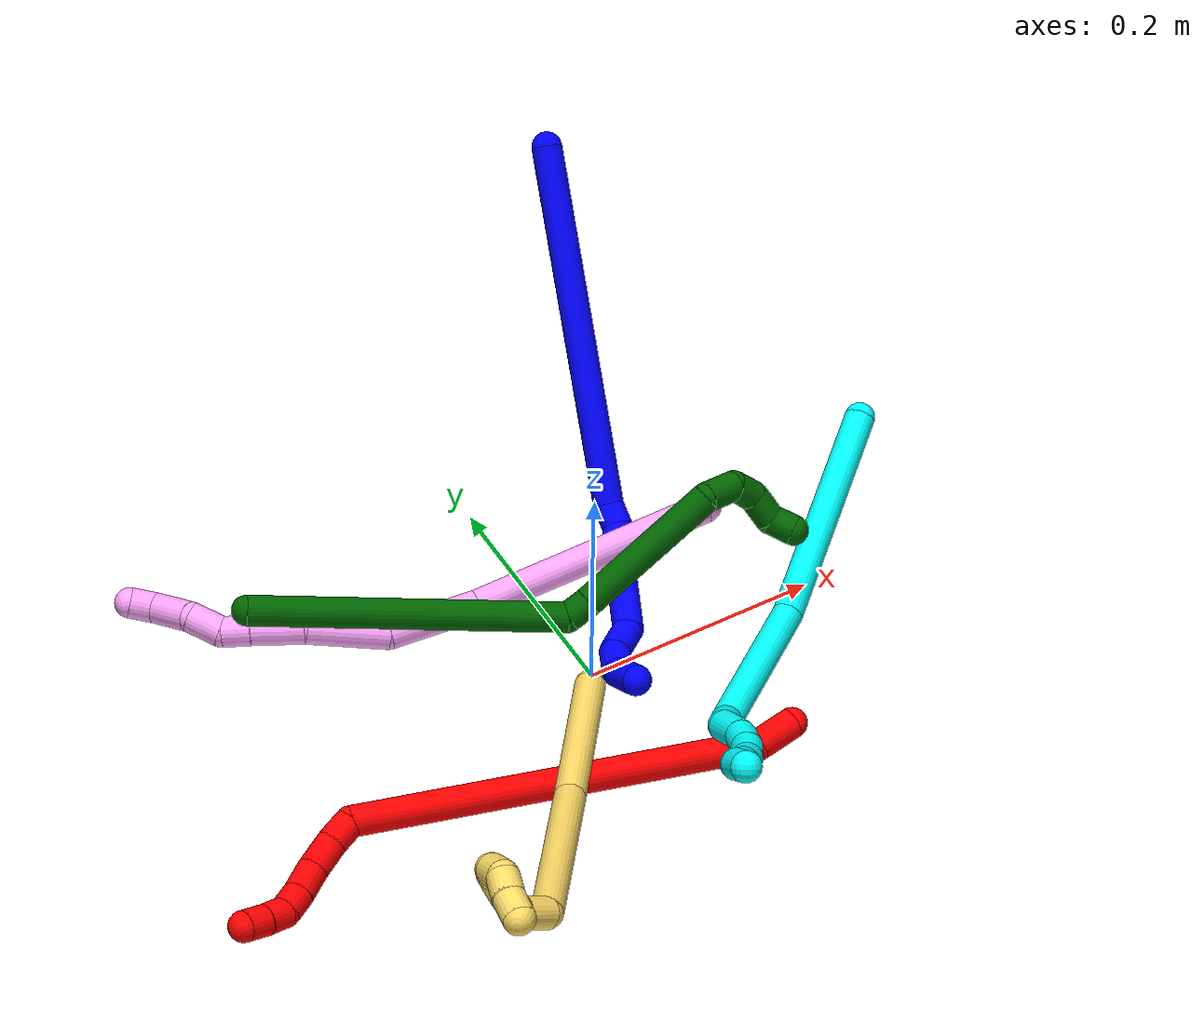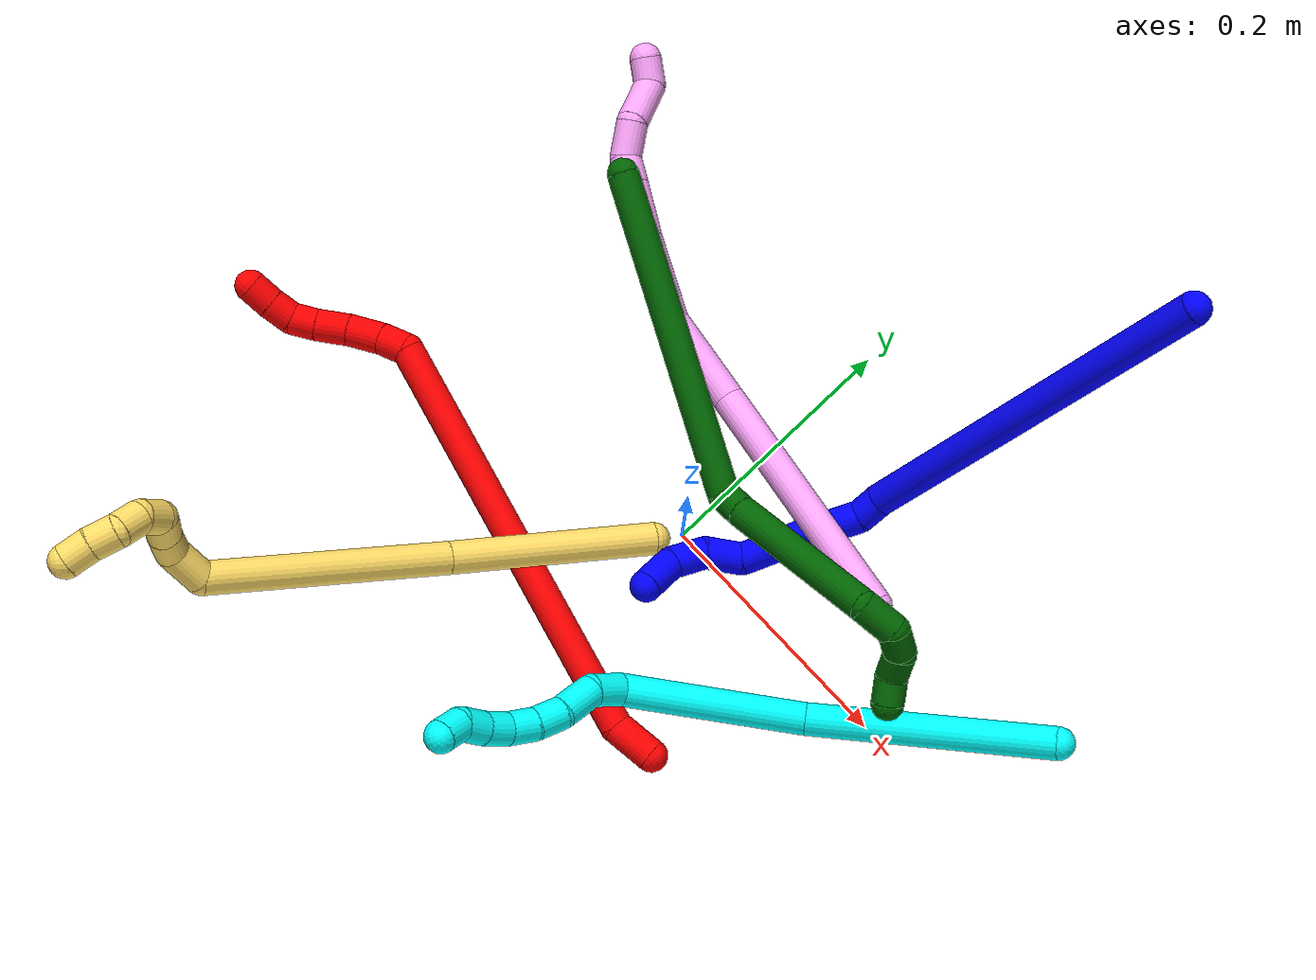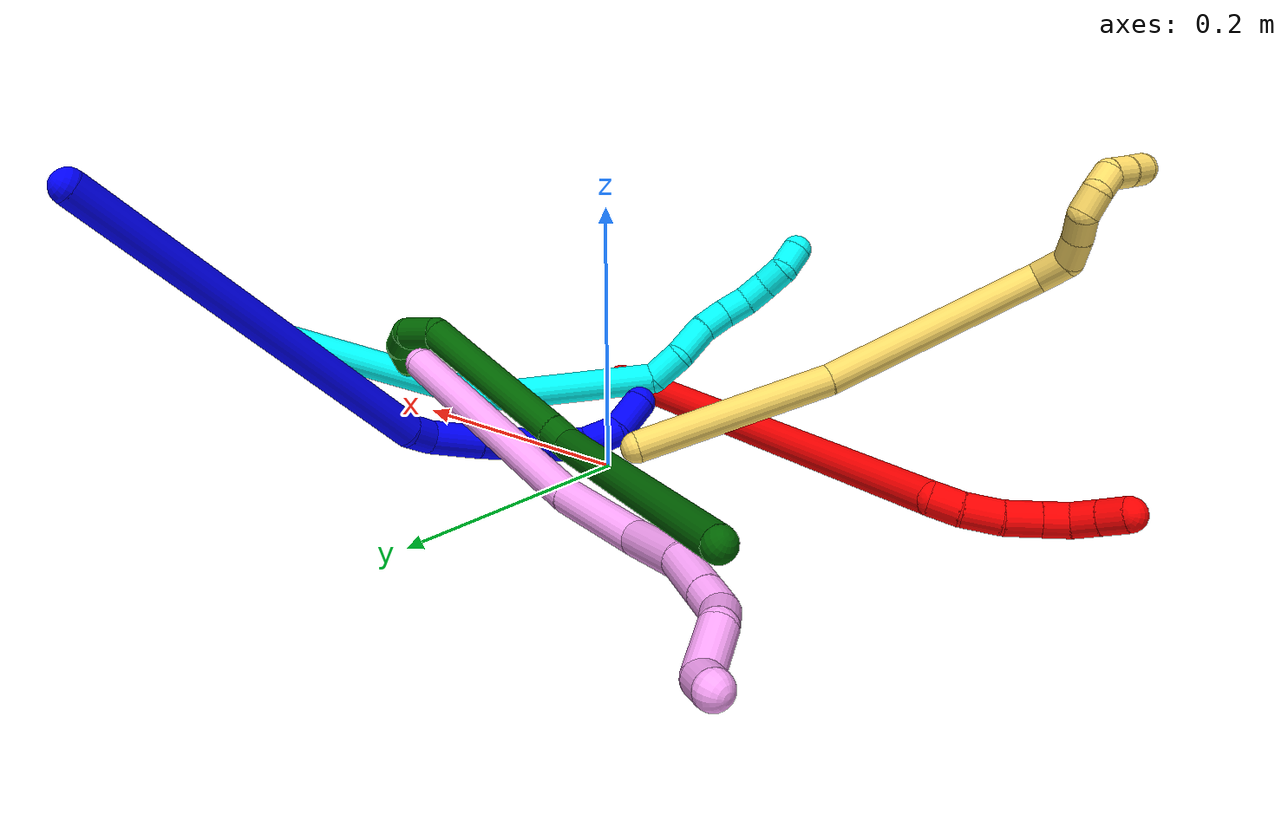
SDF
<sdf version="1.7">
 <world name="default">
  <plugin name="TubeGeneratorPlugin" filename="libtube_generator_plugin.so"/>
  <model name="photoneo_s_sensor">
   <static>1</static>
   <pose>0 0 2 1.57079 1.57079 3.14159</pose>
   <link name="link">
    <inertial><mass>0.1</mass></inertial>
    <sensor name="sensor" type="depth">
     <update_rate>30</update_rate>
     <camera>
      <horizontal_fov>1.22</horizontal_fov>
      <image><width>1920</width><height>1200</height><format>B8G8R8</format></image>
      <clip><near>0.1</near><far>4</far></clip>
      <depth_camera><output>points</output></depth_camera>
     </camera>
     <plugin name="camera_plugin" filename="libgazebo_ros_depth_camera.so">
      <baseline>0.2</baseline>
      <alwaysOn>1</alwaysOn>
      <updateRate>0.0</updateRate>
      <cameraName>camera_ir</cameraName>
      <imageTopicName>/camera/color/image_raw</imageTopicName>
      <cameraInfoTopicName>/camera/color/camera_info</cameraInfoTopicName>
      <depthImageTopicName>/camera/depth/image_raw</depthImageTopicName>
      <depthImageCameraInfoTopicName>/camera/depth/camera_info</depthImageCameraInfoTopicName>
      <pointCloudTopicName>/camera/depth/points</pointCloudTopicName>
      <frameName>fr_optical</frameName>
      <pointCloudCutoff>0.1</pointCloudCutoff>
      <pointCloudCutoffMax>2.0</pointCloudCutoffMax>
      <distortionK1>0</distortionK1>
      <distortionK2>0</distortionK2>
      <distortionK3>0</distortionK3>
      <distortionT1>0</distortionT1>
      <distortionT2>0</distortionT2>
      <CxPrime>0</CxPrime>
      <Cx>0</Cx>
      <Cy>0</Cy>
      <focalLength>0</focalLength>
      <hackBaseline>0</hackBaseline>
     </plugin>
    </sensor>
   </link>
  </model>
  <gravity>0 0 -9.8</gravity>
  <magnetic_field>6e-06 2.3e-05 -4.2e-05</magnetic_field>
  <atmosphere type="adiabatic"/>
  <physics name="default_physics" default="0" type="ode">
   <max_step_size>0.003</max_step_size>
   <real_time_factor>1</real_time_factor>
   <real_time_update_rate>1000</real_time_update_rate>
   <max_contacts>10000</max_contacts>
   <ode>
    <solver>
     <type>quick</type>
     <iters>100</iters>
     <sor>1.3</sor>
     <use_dynamic_moi_rescaling>0</use_dynamic_moi_rescaling>
    </solver>
    <constraints>
     <contact_max_correcting_vel>0</contact_max_correcting_vel>
     <contact_surface_layer>0.001</contact_surface_layer>
     <cfm>0</cfm>
     <erp>0.2</erp>
    </constraints>
   </ode>
  </physics>
  <scene><ambient>0.4 0.4 0.4 1</ambient><background>0.7 0.7 0.7 1</background><shadows>0</shadows></scene>
  <audio><device>default</device></audio>
  <spherical_coordinates>
   <surface_model>EARTH_WGS84</surface_model>
   <latitude_deg>0</latitude_deg>
   <longitude_deg>0</longitude_deg>
   <elevation>0</elevation>
   <heading_deg>0</heading_deg>
  </spherical_coordinates>
  <model name="bin">
   <static>1</static>
   <link name="bottom">
    <collision name="collision-bottom">
     <pose>0 0 -0.01 0 -0 0</pose>
     <geometry><box><size>0.8 0.6 0.02</size></box></geometry>
     <surface>
      <friction><ode><mu>100</mu><mu2>100</mu2></ode></friction>
      <contact><collide_bitmask>65535</collide_bitmask></contact>
     </surface>
    </collision>
   </link>
   <link name="west_wall">
    <collision name="collision-west_wall">
     <pose>-0.41 0 0.1 0 -0 0</pose>
     <geometry><box><size>0.02 0.6 0.2</size></box></geometry>
     <surface>
      <friction><ode><mu>100</mu><mu2>100</mu2></ode></friction>
      <contact><collide_bitmask>65535</collide_bitmask></contact>
     </surface>
    </collision>
   </link>
   <link name="east_wall">
    <collision name="collision-east_wall">
     <pose>0.41 0 0.1 0 -0 0</pose>
     <geometry><box><size>0.02 0.6 0.2</size></box></geometry>
     <surface>
      <friction><ode><mu>100</mu><mu2>100</mu2></ode></friction>
      <contact><collide_bitmask>65535</collide_bitmask></contact>
     </surface>
    </collision>
   </link>
   <link name="south_wall">
    <collision name="collision-south_wall">
     <pose>0 -0.31 0.1 0 -0 0</pose>
     <geometry><box><size>0.8 0.02 0.2</size></box></geometry>
     <surface>
      <friction><ode><mu>100</mu><mu2>100</mu2></ode></friction>
      <contact><collide_bitmask>65535</collide_bitmask></contact>
     </surface>
    </collision>
   </link>
   <link name="north_wall">
    <collision name="collision-north_wall">
     <pose>0 0.31 0.1 0 -0 0</pose>
     <geometry><box><size>0.8 0.02 0.2</size></box></geometry>
     <surface>
      <friction><ode><mu>100</mu><mu2>100</mu2></ode></friction>
      <contact><collide_bitmask>65535</collide_bitmask></contact>
     </surface>
    </collision>
   </link>
  </model>
  <model name="1">
   <static>0</static>
   <link name="1">
    <collision name="collision-cylinder-e_1_1_4">
     <pose>-0.004018 0.023213 -0.146295 -2.98423 -0.027121 0.340684</pose>
     <geometry><cylinder><radius>0.0125</radius><length>0.296358</length></cylinder></geometry>
     <surface>
      <friction><ode><mu>1.16</mu><mu2>1.16</mu2><slip1>0</slip1><slip2>0</slip2></ode></friction>
      <contact><ode><kp>1e+06</kp><kd>1</kd><max_vel>0</max_vel><min_depth>0.001</min_depth></ode></contact>
     </surface>
    </collision>
    <visual name="visual-cylinder-e_1_1_4">
     <pose>-0.004018 0.023213 -0.146295 -2.98423 -0.027121 0.340684</pose>
     <geometry><cylinder><radius>0.0125</radius><length>0.296358</length></cylinder></geometry>
     <material><ambient>0 0 1 1</ambient></material>
    </visual>
    <collision name="collision-cylinder-e_2_4_5">
     <pose>-0.006138 0.045737 -0.302384 3.07143 0.191033 2.43936</pose>
     <geometry><cylinder><radius>0.0125</radius><length>0.020002</length></cylinder></geometry>
     <surface>
      <friction><ode><mu>1.16</mu><mu2>1.16</mu2><slip1>0</slip1><slip2>0</slip2></ode></friction>
      <contact><ode><kp>1e+06</kp><kd>1</kd><max_vel>0</max_vel><min_depth>0.001</min_depth></ode></contact>
     </surface>
    </collision>
    <visual name="visual-cylinder-e_2_4_5">
     <pose>-0.006138 0.045737 -0.302384 3.07143 0.191033 2.43936</pose>
     <geometry><cylinder><radius>0.0125</radius><length>0.020002</length></cylinder></geometry>
     <material><ambient>0 0 1 1</ambient></material>
    </visual>
    <collision name="collision-cylinder-e_3_5_6">
     <pose>-0.006481 0.037928 -0.330667 2.77396 -0.112707 -0.589214</pose>
     <geometry><cylinder><radius>0.0125</radius><length>0.039878</length></cylinder></geometry>
     <surface>
      <friction><ode><mu>1.16</mu><mu2>1.16</mu2><slip1>0</slip1><slip2>0</slip2></ode></friction>
      <contact><ode><kp>1e+06</kp><kd>1</kd><max_vel>0</max_vel><min_depth>0.001</min_depth></ode></contact>
     </surface>
    </collision>
    <visual name="visual-cylinder-e_3_5_6">
     <pose>-0.006481 0.037928 -0.330667 2.77396 -0.112707 -0.589214</pose>
     <geometry><cylinder><radius>0.0125</radius><length>0.039878</length></cylinder></geometry>
     <material><ambient>0 0 1 1</ambient></material>
    </visual>
    <collision name="collision-cylinder-e_4_6_7">
     <pose>-0.010253 0.020096 -0.37478 2.74567 -0.055008 -0.272603</pose>
     <geometry><cylinder><radius>0.0125</radius><length>0.055629</length></cylinder></geometry>
     <surface>
      <friction><ode><mu>1.16</mu><mu2>1.16</mu2><slip1>0</slip1><slip2>0</slip2></ode></friction>
      <contact><ode><kp>1e+06</kp><kd>1</kd><max_vel>0</max_vel><min_depth>0.001</min_depth></ode></contact>
     </surface>
    </collision>
    <visual name="visual-cylinder-e_4_6_7">
     <pose>-0.010253 0.020096 -0.37478 2.74567 -0.055008 -0.272603</pose>
     <geometry><cylinder><radius>0.0125</radius><length>0.055629</length></cylinder></geometry>
     <material><ambient>0 0 1 1</ambient></material>
    </visual>
    <collision name="collision-cylinder-e_5_7_8">
     <pose>-0.018827 0.000609 -0.409309 2.36345 -0.513086 -1.13842</pose>
     <geometry><cylinder><radius>0.0125</radius><length>0.028703</length></cylinder></geometry>
     <surface>
      <friction><ode><mu>1.16</mu><mu2>1.16</mu2><slip1>0</slip1><slip2>0</slip2></ode></friction>
      <contact><ode><kp>1e+06</kp><kd>1</kd><max_vel>0</max_vel><min_depth>0.001</min_depth></ode></contact>
     </surface>
    </collision>
    <visual name="visual-cylinder-e_5_7_8">
     <pose>-0.018827 0.000609 -0.409309 2.36345 -0.513086 -1.13842</pose>
     <geometry><cylinder><radius>0.0125</radius><length>0.028703</length></cylinder></geometry>
     <material><ambient>0 0 1 1</ambient></material>
    </visual>
    <collision name="collision-cylinder-e_6_8_9">
     <pose>-0.026076 -0.018707 -0.427609 2.29886 -0.014482 -0.032307</pose>
     <geometry><cylinder><radius>0.0125</radius><length>0.028238</length></cylinder></geometry>
     <surface>
      <friction><ode><mu>1.16</mu><mu2>1.16</mu2><slip1>0</slip1><slip2>0</slip2></ode></friction>
      <contact><ode><kp>1e+06</kp><kd>1</kd><max_vel>0</max_vel><min_depth>0.001</min_depth></ode></contact>
     </surface>
    </collision>
    <visual name="visual-cylinder-e_6_8_9">
     <pose>-0.026076 -0.018707 -0.427609 2.29886 -0.014482 -0.032307</pose>
     <geometry><cylinder><radius>0.0125</radius><length>0.028238</length></cylinder></geometry>
     <material><ambient>0 0 1 1</ambient></material>
    </visual>
    <collision name="collision-cylinder-e_7_9_2">
     <pose>-0.019654 -0.041898 -0.443264 2.0303 0.438882 0.689705</pose>
     <geometry><cylinder><radius>0.0125</radius><length>0.031192</length></cylinder></geometry>
     <surface>
      <friction><ode><mu>1.16</mu><mu2>1.16</mu2><slip1>0</slip1><slip2>0</slip2></ode></friction>
      <contact><ode><kp>1e+06</kp><kd>1</kd><max_vel>0</max_vel><min_depth>0.001</min_depth></ode></contact>
     </surface>
    </collision>
    <visual name="visual-cylinder-e_7_9_2">
     <pose>-0.019654 -0.041898 -0.443264 2.0303 0.438882 0.689705</pose>
     <geometry><cylinder><radius>0.0125</radius><length>0.031192</length></cylinder></geometry>
     <material><ambient>0 0 1 1</ambient></material>
    </visual>
    <collision name="collision-sphere-2">
     <pose>-0.013027 -0.054552 -0.449525 0 -0 0</pose>
     <geometry><sphere><radius>0.0125</radius></sphere></geometry>
     <surface>
      <friction><ode><mu>1.16</mu><mu2>1.16</mu2><slip1>0</slip1><slip2>0</slip2></ode></friction>
      <contact><ode><kp>1e+06</kp><kd>1</kd><max_vel>0</max_vel><min_depth>0.001</min_depth></ode></contact>
     </surface>
    </collision>
    <visual name="visual-sphere-2">
     <pose>-0.013027 -0.054552 -0.449525 0 -0 0</pose>
     <geometry><sphere><radius>0.0125</radius></sphere></geometry>
     <material><ambient>0 0 1 1</ambient></material>
    </visual>
    <collision name="collision-sphere-9">
     <pose>-0.026281 -0.029245 -0.437003 0 -0 0</pose>
     <geometry><sphere><radius>0.0125</radius></sphere></geometry>
     <surface>
      <friction><ode><mu>1.16</mu><mu2>1.16</mu2><slip1>0</slip1><slip2>0</slip2></ode></friction>
      <contact><ode><kp>1e+06</kp><kd>1</kd><max_vel>0</max_vel><min_depth>0.001</min_depth></ode></contact>
     </surface>
    </collision>
    <visual name="visual-sphere-9">
     <pose>-0.026281 -0.029245 -0.437003 0 -0 0</pose>
     <geometry><sphere><radius>0.0125</radius></sphere></geometry>
     <material><ambient>0 0 1 1</ambient></material>
    </visual>
    <collision name="collision-sphere-4">
     <pose>-0.008037 0.046425 -0.292589 0 -0 0</pose>
     <geometry><sphere><radius>0.0125</radius></sphere></geometry>
     <surface>
      <friction><ode><mu>1.16</mu><mu2>1.16</mu2><slip1>0</slip1><slip2>0</slip2></ode></friction>
      <contact><ode><kp>1e+06</kp><kd>1</kd><max_vel>0</max_vel><min_depth>0.001</min_depth></ode></contact>
     </surface>
    </collision>
    <visual name="visual-sphere-4">
     <pose>-0.008037 0.046425 -0.292589 0 -0 0</pose>
     <geometry><sphere><radius>0.0125</radius></sphere></geometry>
     <material><ambient>0 0 1 1</ambient></material>
    </visual>
    <collision name="collision-sphere-1">
     <geometry><sphere><radius>0.0125</radius></sphere></geometry>
     <surface>
      <friction><ode><mu>1.16</mu><mu2>1.16</mu2><slip1>0</slip1><slip2>0</slip2></ode></friction>
      <contact><ode><kp>1e+06</kp><kd>1</kd><max_vel>0</max_vel><min_depth>0.001</min_depth></ode></contact>
     </surface>
    </collision>
    <visual name="visual-sphere-1">
     <geometry><sphere><radius>0.0125</radius></sphere></geometry>
     <material><ambient>0 0 1 1</ambient></material>
    </visual>
    <collision name="collision-sphere-8">
     <pose>-0.025872 -0.008168 -0.418215 0 -0 0</pose>
     <geometry><sphere><radius>0.0125</radius></sphere></geometry>
     <surface>
      <friction><ode><mu>1.16</mu><mu2>1.16</mu2><slip1>0</slip1><slip2>0</slip2></ode></friction>
      <contact><ode><kp>1e+06</kp><kd>1</kd><max_vel>0</max_vel><min_depth>0.001</min_depth></ode></contact>
     </surface>
    </collision>
    <visual name="visual-sphere-8">
     <pose>-0.025872 -0.008168 -0.418215 0 -0 0</pose>
     <geometry><sphere><radius>0.0125</radius></sphere></geometry>
     <material><ambient>0 0 1 1</ambient></material>
    </visual>
    <collision name="collision-sphere-5">
     <pose>-0.004239 0.045048 -0.312179 0 -0 0</pose>
     <geometry><sphere><radius>0.0125</radius></sphere></geometry>
     <surface>
      <friction><ode><mu>1.16</mu><mu2>1.16</mu2><slip1>0</slip1><slip2>0</slip2></ode></friction>
      <contact><ode><kp>1e+06</kp><kd>1</kd><max_vel>0</max_vel><min_depth>0.001</min_depth></ode></contact>
     </surface>
    </collision>
    <visual name="visual-sphere-5">
     <pose>-0.004239 0.045048 -0.312179 0 -0 0</pose>
     <geometry><sphere><radius>0.0125</radius></sphere></geometry>
     <material><ambient>0 0 1 1</ambient></material>
    </visual>
    <collision name="collision-sphere-6">
     <pose>-0.008724 0.030807 -0.349156 0 -0 0</pose>
     <geometry><sphere><radius>0.0125</radius></sphere></geometry>
     <surface>
      <friction><ode><mu>1.16</mu><mu2>1.16</mu2><slip1>0</slip1><slip2>0</slip2></ode></friction>
      <contact><ode><kp>1e+06</kp><kd>1</kd><max_vel>0</max_vel><min_depth>0.001</min_depth></ode></contact>
     </surface>
    </collision>
    <visual name="visual-sphere-6">
     <pose>-0.008724 0.030807 -0.349156 0 -0 0</pose>
     <geometry><sphere><radius>0.0125</radius></sphere></geometry>
     <material><ambient>0 0 1 1</ambient></material>
    </visual>
    <collision name="collision-sphere-7">
     <pose>-0.011782 0.009386 -0.400404 0 -0 0</pose>
     <geometry><sphere><radius>0.0125</radius></sphere></geometry>
     <surface>
      <friction><ode><mu>1.16</mu><mu2>1.16</mu2><slip1>0</slip1><slip2>0</slip2></ode></friction>
      <contact><ode><kp>1e+06</kp><kd>1</kd><max_vel>0</max_vel><min_depth>0.001</min_depth></ode></contact>
     </surface>
    </collision>
    <visual name="visual-sphere-7">
     <pose>-0.011782 0.009386 -0.400404 0 -0 0</pose>
     <geometry><sphere><radius>0.0125</radius></sphere></geometry>
     <material><ambient>0 0 1 1</ambient></material>
    </visual>
    <inertial>
     <pose>-0.008064 0.017214 -0.242177 0 -0 0</pose>
     <mass>0.5</mass>
     <inertia>
      <ixx>0.002801</ixx>
      <ixy>0</ixy>
      <ixz>0</ixz>
      <iyy>-0.001331</iyy>
      <iyz>0</iyz>
      <izz>-0.0003</izz>
     </inertia>
    </inertial>
   </link>
   <pose>0.145542 0.329707 0.245091 -0.96862 -0.152689 -0.386949</pose>
  </model>
  <model name="2">
   <static>0</static>
   <link name="2">
    <collision name="collision-cylinder-e_1_1_4">
     <pose>-0.017068 -0.001013 0.002353 0.406525 -1.42183 -0.351312</pose>
     <geometry><cylinder><radius>0.0125</radius><length>0.034519</length></cylinder></geometry>
     <surface>
      <friction><ode><mu>1.16</mu><mu2>1.16</mu2><slip1>0</slip1><slip2>0</slip2></ode></friction>
      <contact><ode><kp>1e+06</kp><kd>1</kd><max_vel>0</max_vel><min_depth>0.001</min_depth></ode></contact>
     </surface>
    </collision>
    <visual name="visual-cylinder-e_1_1_4">
     <pose>-0.017068 -0.001013 0.002353 0.406525 -1.42183 -0.351312</pose>
     <geometry><cylinder><radius>0.0125</radius><length>0.034519</length></cylinder></geometry>
     <material><ambient>1 0 0 1</ambient></material>
    </visual>
    <collision name="collision-cylinder-e_2_4_5">
     <pose>-0.193166 -0.010206 -0.036935 2.94762 -1.31002 -2.88961</pose>
     <geometry><cylinder><radius>0.0125</radius><length>0.329189</length></cylinder></geometry>
     <surface>
      <friction><ode><mu>1.16</mu><mu2>1.16</mu2><slip1>0</slip1><slip2>0</slip2></ode></friction>
      <contact><ode><kp>1e+06</kp><kd>1</kd><max_vel>0</max_vel><min_depth>0.001</min_depth></ode></contact>
     </surface>
    </collision>
    <visual name="visual-cylinder-e_2_4_5">
     <pose>-0.193166 -0.010206 -0.036935 2.94762 -1.31002 -2.88961</pose>
     <geometry><cylinder><radius>0.0125</radius><length>0.329189</length></cylinder></geometry>
     <material><ambient>1 0 0 1</ambient></material>
    </visual>
    <collision name="collision-cylinder-e_3_5_6">
     <pose>-0.362499 -0.019663 -0.074167 0.281811 -1.15162 -0.183654</pose>
     <geometry><cylinder><radius>0.0125</radius><length>0.022558</length></cylinder></geometry>
     <surface>
      <friction><ode><mu>1.16</mu><mu2>1.16</mu2><slip1>0</slip1><slip2>0</slip2></ode></friction>
      <contact><ode><kp>1e+06</kp><kd>1</kd><max_vel>0</max_vel><min_depth>0.001</min_depth></ode></contact>
     </surface>
    </collision>
    <visual name="visual-cylinder-e_3_5_6">
     <pose>-0.362499 -0.019663 -0.074167 0.281811 -1.15162 -0.183654</pose>
     <geometry><cylinder><radius>0.0125</radius><length>0.022558</length></cylinder></geometry>
     <material><ambient>1 0 0 1</ambient></material>
    </visual>
    <collision name="collision-cylinder-e_4_6_7">
     <pose>-0.3848 -0.020674 -0.062804 -0.038235 -1.04525 0.022027</pose>
     <geometry><cylinder><radius>0.0125</radius><length>0.02774</length></cylinder></geometry>
     <surface>
      <friction><ode><mu>1.16</mu><mu2>1.16</mu2><slip1>0</slip1><slip2>0</slip2></ode></friction>
      <contact><ode><kp>1e+06</kp><kd>1</kd><max_vel>0</max_vel><min_depth>0.001</min_depth></ode></contact>
     </surface>
    </collision>
    <visual name="visual-cylinder-e_4_6_7">
     <pose>-0.3848 -0.020674 -0.062804 -0.038235 -1.04525 0.022027</pose>
     <geometry><cylinder><radius>0.0125</radius><length>0.02774</length></cylinder></geometry>
     <material><ambient>1 0 0 1</ambient></material>
    </visual>
    <collision name="collision-cylinder-e_5_7_8">
     <pose>-0.407147 -0.018131 -0.048515 -0.300872 -0.932307 0.152237</pose>
     <geometry><cylinder><radius>0.0125</radius><length>0.025776</length></cylinder></geometry>
     <surface>
      <friction><ode><mu>1.16</mu><mu2>1.16</mu2><slip1>0</slip1><slip2>0</slip2></ode></friction>
      <contact><ode><kp>1e+06</kp><kd>1</kd><max_vel>0</max_vel><min_depth>0.001</min_depth></ode></contact>
     </surface>
    </collision>
    <visual name="visual-cylinder-e_5_7_8">
     <pose>-0.407147 -0.018131 -0.048515 -0.300872 -0.932307 0.152237</pose>
     <geometry><cylinder><radius>0.0125</radius><length>0.025776</length></cylinder></geometry>
     <material><ambient>1 0 0 1</ambient></material>
    </visual>
    <collision name="collision-cylinder-e_6_8_9">
     <pose>-0.426074 -0.01391 -0.03629 -0.378612 -1.02062 0.213684</pose>
     <geometry><cylinder><radius>0.0125</radius><length>0.020126</length></cylinder></geometry>
     <surface>
      <friction><ode><mu>1.16</mu><mu2>1.16</mu2><slip1>0</slip1><slip2>0</slip2></ode></friction>
      <contact><ode><kp>1e+06</kp><kd>1</kd><max_vel>0</max_vel><min_depth>0.001</min_depth></ode></contact>
     </surface>
    </collision>
    <visual name="visual-cylinder-e_6_8_9">
     <pose>-0.426074 -0.01391 -0.03629 -0.378612 -1.02062 0.213684</pose>
     <geometry><cylinder><radius>0.0125</radius><length>0.020126</length></cylinder></geometry>
     <material><ambient>1 0 0 1</ambient></material>
    </visual>
    <collision name="collision-cylinder-e_7_9_10">
     <pose>-0.444028 -0.00851 -0.030571 -1.33496 -1.20845 0.996624</pose>
     <geometry><cylinder><radius>0.0125</radius><length>0.020054</length></cylinder></geometry>
     <surface>
      <friction><ode><mu>1.16</mu><mu2>1.16</mu2><slip1>0</slip1><slip2>0</slip2></ode></friction>
      <contact><ode><kp>1e+06</kp><kd>1</kd><max_vel>0</max_vel><min_depth>0.001</min_depth></ode></contact>
     </surface>
    </collision>
    <visual name="visual-cylinder-e_7_9_10">
     <pose>-0.444028 -0.00851 -0.030571 -1.33496 -1.20845 0.996624</pose>
     <geometry><cylinder><radius>0.0125</radius><length>0.020054</length></cylinder></geometry>
     <material><ambient>1 0 0 1</ambient></material>
    </visual>
    <collision name="collision-cylinder-e_8_10_2">
     <pose>-0.462799 -0.001575 -0.029765 -1.57787 -1.21617 1.22282</pose>
     <geometry><cylinder><radius>0.0125</radius><length>0.020038</length></cylinder></geometry>
     <surface>
      <friction><ode><mu>1.16</mu><mu2>1.16</mu2><slip1>0</slip1><slip2>0</slip2></ode></friction>
      <contact><ode><kp>1e+06</kp><kd>1</kd><max_vel>0</max_vel><min_depth>0.001</min_depth></ode></contact>
     </surface>
    </collision>
    <visual name="visual-cylinder-e_8_10_2">
     <pose>-0.462799 -0.001575 -0.029765 -1.57787 -1.21617 1.22282</pose>
     <geometry><cylinder><radius>0.0125</radius><length>0.020038</length></cylinder></geometry>
     <material><ambient>1 0 0 1</ambient></material>
    </visual>
    <collision name="collision-sphere-2">
     <pose>-0.472195 0.001904 -0.02979 0 -0 0</pose>
     <geometry><sphere><radius>0.0125</radius></sphere></geometry>
     <surface>
      <friction><ode><mu>1.16</mu><mu2>1.16</mu2><slip1>0</slip1><slip2>0</slip2></ode></friction>
      <contact><ode><kp>1e+06</kp><kd>1</kd><max_vel>0</max_vel><min_depth>0.001</min_depth></ode></contact>
     </surface>
    </collision>
    <visual name="visual-sphere-2">
     <pose>-0.472195 0.001904 -0.02979 0 -0 0</pose>
     <geometry><sphere><radius>0.0125</radius></sphere></geometry>
     <material><ambient>1 0 0 1</ambient></material>
    </visual>
    <collision name="collision-sphere-10">
     <pose>-0.453404 -0.005054 -0.02974 0 -0 0</pose>
     <geometry><sphere><radius>0.0125</radius></sphere></geometry>
     <surface>
      <friction><ode><mu>1.16</mu><mu2>1.16</mu2><slip1>0</slip1><slip2>0</slip2></ode></friction>
      <contact><ode><kp>1e+06</kp><kd>1</kd><max_vel>0</max_vel><min_depth>0.001</min_depth></ode></contact>
     </surface>
    </collision>
    <visual name="visual-sphere-10">
     <pose>-0.453404 -0.005054 -0.02974 0 -0 0</pose>
     <geometry><sphere><radius>0.0125</radius></sphere></geometry>
     <material><ambient>1 0 0 1</ambient></material>
    </visual>
    <collision name="collision-sphere-9">
     <pose>-0.434652 -0.011965 -0.031401 0 -0 0</pose>
     <geometry><sphere><radius>0.0125</radius></sphere></geometry>
     <surface>
      <friction><ode><mu>1.16</mu><mu2>1.16</mu2><slip1>0</slip1><slip2>0</slip2></ode></friction>
      <contact><ode><kp>1e+06</kp><kd>1</kd><max_vel>0</max_vel><min_depth>0.001</min_depth></ode></contact>
     </surface>
    </collision>
    <visual name="visual-sphere-9">
     <pose>-0.434652 -0.011965 -0.031401 0 -0 0</pose>
     <geometry><sphere><radius>0.0125</radius></sphere></geometry>
     <material><ambient>1 0 0 1</ambient></material>
    </visual>
    <collision name="collision-sphere-4">
     <pose>-0.034137 -0.002026 0.004706 0 -0 0</pose>
     <geometry><sphere><radius>0.0125</radius></sphere></geometry>
     <surface>
      <friction><ode><mu>1.16</mu><mu2>1.16</mu2><slip1>0</slip1><slip2>0</slip2></ode></friction>
      <contact><ode><kp>1e+06</kp><kd>1</kd><max_vel>0</max_vel><min_depth>0.001</min_depth></ode></contact>
     </surface>
    </collision>
    <visual name="visual-sphere-4">
     <pose>-0.034137 -0.002026 0.004706 0 -0 0</pose>
     <geometry><sphere><radius>0.0125</radius></sphere></geometry>
     <material><ambient>1 0 0 1</ambient></material>
    </visual>
    <collision name="collision-sphere-1">
     <geometry><sphere><radius>0.0125</radius></sphere></geometry>
     <surface>
      <friction><ode><mu>1.16</mu><mu2>1.16</mu2><slip1>0</slip1><slip2>0</slip2></ode></friction>
      <contact><ode><kp>1e+06</kp><kd>1</kd><max_vel>0</max_vel><min_depth>0.001</min_depth></ode></contact>
     </surface>
    </collision>
    <visual name="visual-sphere-1">
     <geometry><sphere><radius>0.0125</radius></sphere></geometry>
     <material><ambient>1 0 0 1</ambient></material>
    </visual>
    <collision name="collision-sphere-8">
     <pose>-0.417496 -0.015855 -0.041179 0 -0 0</pose>
     <geometry><sphere><radius>0.0125</radius></sphere></geometry>
     <surface>
      <friction><ode><mu>1.16</mu><mu2>1.16</mu2><slip1>0</slip1><slip2>0</slip2></ode></friction>
      <contact><ode><kp>1e+06</kp><kd>1</kd><max_vel>0</max_vel><min_depth>0.001</min_depth></ode></contact>
     </surface>
    </collision>
    <visual name="visual-sphere-8">
     <pose>-0.417496 -0.015855 -0.041179 0 -0 0</pose>
     <geometry><sphere><radius>0.0125</radius></sphere></geometry>
     <material><ambient>1 0 0 1</ambient></material>
    </visual>
    <collision name="collision-sphere-5">
     <pose>-0.352196 -0.018386 -0.078576 0 -0 0</pose>
     <geometry><sphere><radius>0.0125</radius></sphere></geometry>
     <surface>
      <friction><ode><mu>1.16</mu><mu2>1.16</mu2><slip1>0</slip1><slip2>0</slip2></ode></friction>
      <contact><ode><kp>1e+06</kp><kd>1</kd><max_vel>0</max_vel><min_depth>0.001</min_depth></ode></contact>
     </surface>
    </collision>
    <visual name="visual-sphere-5">
     <pose>-0.352196 -0.018386 -0.078576 0 -0 0</pose>
     <geometry><sphere><radius>0.0125</radius></sphere></geometry>
     <material><ambient>1 0 0 1</ambient></material>
    </visual>
    <collision name="collision-sphere-6">
     <pose>-0.372801 -0.02094 -0.069757 0 -0 0</pose>
     <geometry><sphere><radius>0.0125</radius></sphere></geometry>
     <surface>
      <friction><ode><mu>1.16</mu><mu2>1.16</mu2><slip1>0</slip1><slip2>0</slip2></ode></friction>
      <contact><ode><kp>1e+06</kp><kd>1</kd><max_vel>0</max_vel><min_depth>0.001</min_depth></ode></contact>
     </surface>
    </collision>
    <visual name="visual-sphere-6">
     <pose>-0.372801 -0.02094 -0.069757 0 -0 0</pose>
     <geometry><sphere><radius>0.0125</radius></sphere></geometry>
     <material><ambient>1 0 0 1</ambient></material>
    </visual>
    <collision name="collision-sphere-7">
     <pose>-0.396798 -0.020408 -0.055851 0 -0 0</pose>
     <geometry><sphere><radius>0.0125</radius></sphere></geometry>
     <surface>
      <friction><ode><mu>1.16</mu><mu2>1.16</mu2><slip1>0</slip1><slip2>0</slip2></ode></friction>
      <contact><ode><kp>1e+06</kp><kd>1</kd><max_vel>0</max_vel><min_depth>0.001</min_depth></ode></contact>
     </surface>
    </collision>
    <visual name="visual-sphere-7">
     <pose>-0.396798 -0.020408 -0.055851 0 -0 0</pose>
     <geometry><sphere><radius>0.0125</radius></sphere></geometry>
     <material><ambient>1 0 0 1</ambient></material>
    </visual>
    <inertial>
     <pose>-0.240554 -0.010722 -0.037366 0 -0 0</pose>
     <mass>0.5</mass>
     <inertia>
      <ixx>-0.000968</ixx>
      <ixy>0</ixy>
      <ixz>0</ixz>
      <iyy>0.002801</iyy>
      <iyz>0</iyz>
      <izz>0.003044</izz>
     </inertia>
    </inertial>
   </link>
   <pose>0.105414 -0.13255 0.01505 1.89915 -0.003524 0.009858</pose>
  </model>
  <model name="3">
   <static>0</static>
   <link name="3">
    <collision name="collision-cylinder-e_1_1_4">
     <pose>-0.060215 -0.00586 -0.072539 3.06098 -0.691232 -2.91852</pose>
     <geometry><cylinder><radius>0.0125</radius><length>0.188915</length></cylinder></geometry>
     <surface>
      <friction><ode><mu>1.16</mu><mu2>1.16</mu2><slip1>0</slip1><slip2>0</slip2></ode></friction>
      <contact><ode><kp>1e+06</kp><kd>1</kd><max_vel>0</max_vel><min_depth>0.001</min_depth></ode></contact>
     </surface>
    </collision>
    <visual name="visual-cylinder-e_1_1_4">
     <pose>-0.060215 -0.00586 -0.072539 3.06098 -0.691232 -2.91852</pose>
     <geometry><cylinder><radius>0.0125</radius><length>0.188915</length></cylinder></geometry>
     <material><ambient>0.003922 1 0.996078 1</ambient></material>
    </visual>
    <collision name="collision-cylinder-e_2_4_5">
     <pose>-0.182528 -0.024697 -0.176338 2.74813 -1.07177 -2.49397</pose>
     <geometry><cylinder><radius>0.0125</radius><length>0.141444</length></cylinder></geometry>
     <surface>
      <friction><ode><mu>1.16</mu><mu2>1.16</mu2><slip1>0</slip1><slip2>0</slip2></ode></friction>
      <contact><ode><kp>1e+06</kp><kd>1</kd><max_vel>0</max_vel><min_depth>0.001</min_depth></ode></contact>
     </surface>
    </collision>
    <visual name="visual-cylinder-e_2_4_5">
     <pose>-0.182528 -0.024697 -0.176338 2.74813 -1.07177 -2.49397</pose>
     <geometry><cylinder><radius>0.0125</radius><length>0.141444</length></cylinder></geometry>
     <material><ambient>0.003922 1 0.996078 1</ambient></material>
    </visual>
    <collision name="collision-cylinder-e_3_5_6">
     <pose>-0.256936 -0.044728 -0.206585 1.42833 -1.046 -0.9269</pose>
     <geometry><cylinder><radius>0.0125</radius><length>0.02845</length></cylinder></geometry>
     <surface>
      <friction><ode><mu>1.16</mu><mu2>1.16</mu2><slip1>0</slip1><slip2>0</slip2></ode></friction>
      <contact><ode><kp>1e+06</kp><kd>1</kd><max_vel>0</max_vel><min_depth>0.001</min_depth></ode></contact>
     </surface>
    </collision>
    <visual name="visual-cylinder-e_3_5_6">
     <pose>-0.256936 -0.044728 -0.206585 1.42833 -1.046 -0.9269</pose>
     <geometry><cylinder><radius>0.0125</radius><length>0.02845</length></cylinder></geometry>
     <material><ambient>0.003922 1 0.996078 1</ambient></material>
    </visual>
    <collision name="collision-cylinder-e_4_6_7">
     <pose>-0.27792 -0.065484 -0.205949 1.59822 -0.564151 -0.578987</pose>
     <geometry><cylinder><radius>0.0125</radius><length>0.03244</length></cylinder></geometry>
     <surface>
      <friction><ode><mu>1.16</mu><mu2>1.16</mu2><slip1>0</slip1><slip2>0</slip2></ode></friction>
      <contact><ode><kp>1e+06</kp><kd>1</kd><max_vel>0</max_vel><min_depth>0.001</min_depth></ode></contact>
     </surface>
    </collision>
    <visual name="visual-cylinder-e_4_6_7">
     <pose>-0.27792 -0.065484 -0.205949 1.59822 -0.564151 -0.578987</pose>
     <geometry><cylinder><radius>0.0125</radius><length>0.03244</length></cylinder></geometry>
     <material><ambient>0.003922 1 0.996078 1</ambient></material>
    </visual>
    <collision name="collision-cylinder-e_5_7_8">
     <pose>-0.294604 -0.08756 -0.208345 1.80755 -0.749147 -0.926125</pose>
     <geometry><cylinder><radius>0.0125</radius><length>0.023528</length></cylinder></geometry>
     <surface>
      <friction><ode><mu>1.16</mu><mu2>1.16</mu2><slip1>0</slip1><slip2>0</slip2></ode></friction>
      <contact><ode><kp>1e+06</kp><kd>1</kd><max_vel>0</max_vel><min_depth>0.001</min_depth></ode></contact>
     </surface>
    </collision>
    <visual name="visual-cylinder-e_5_7_8">
     <pose>-0.294604 -0.08756 -0.208345 1.80755 -0.749147 -0.926125</pose>
     <geometry><cylinder><radius>0.0125</radius><length>0.023528</length></cylinder></geometry>
     <material><ambient>0.003922 1 0.996078 1</ambient></material>
    </visual>
    <collision name="collision-cylinder-e_6_8_9">
     <pose>-0.311644 -0.102089 -0.21225 1.86791 -0.951426 -1.21677</pose>
     <geometry><cylinder><radius>0.0125</radius><length>0.022178</length></cylinder></geometry>
     <surface>
      <friction><ode><mu>1.16</mu><mu2>1.16</mu2><slip1>0</slip1><slip2>0</slip2></ode></friction>
      <contact><ode><kp>1e+06</kp><kd>1</kd><max_vel>0</max_vel><min_depth>0.001</min_depth></ode></contact>
     </surface>
    </collision>
    <visual name="visual-cylinder-e_6_8_9">
     <pose>-0.311644 -0.102089 -0.21225 1.86791 -0.951426 -1.21677</pose>
     <geometry><cylinder><radius>0.0125</radius><length>0.022178</length></cylinder></geometry>
     <material><ambient>0.003922 1 0.996078 1</ambient></material>
    </visual>
    <collision name="collision-cylinder-e_7_9_10">
     <pose>-0.330227 -0.112989 -0.213493 1.43637 -1.10621 -0.989513</pose>
     <geometry><cylinder><radius>0.0125</radius><length>0.021372</length></cylinder></geometry>
     <surface>
      <friction><ode><mu>1.16</mu><mu2>1.16</mu2><slip1>0</slip1><slip2>0</slip2></ode></friction>
      <contact><ode><kp>1e+06</kp><kd>1</kd><max_vel>0</max_vel><min_depth>0.001</min_depth></ode></contact>
     </surface>
    </collision>
    <visual name="visual-cylinder-e_7_9_10">
     <pose>-0.330227 -0.112989 -0.213493 1.43637 -1.10621 -0.989513</pose>
     <geometry><cylinder><radius>0.0125</radius><length>0.021372</length></cylinder></geometry>
     <material><ambient>0.003922 1 0.996078 1</ambient></material>
    </visual>
    <collision name="collision-cylinder-e_8_10_11">
     <pose>-0.349556 -0.121107 -0.211257 1.12904 -1.2062 -0.822514</pose>
     <geometry><cylinder><radius>0.0125</radius><length>0.020927</length></cylinder></geometry>
     <surface>
      <friction><ode><mu>1.16</mu><mu2>1.16</mu2><slip1>0</slip1><slip2>0</slip2></ode></friction>
      <contact><ode><kp>1e+06</kp><kd>1</kd><max_vel>0</max_vel><min_depth>0.001</min_depth></ode></contact>
     </surface>
    </collision>
    <visual name="visual-cylinder-e_8_10_11">
     <pose>-0.349556 -0.121107 -0.211257 1.12904 -1.2062 -0.822514</pose>
     <geometry><cylinder><radius>0.0125</radius><length>0.020927</length></cylinder></geometry>
     <material><ambient>0.003922 1 0.996078 1</ambient></material>
    </visual>
    <collision name="collision-cylinder-e_9_11_2">
     <pose>-0.365358 -0.132828 -0.208397 1.42047 -0.619904 -0.537507</pose>
     <geometry><cylinder><radius>0.0125</radius><length>0.020747</length></cylinder></geometry>
     <surface>
      <friction><ode><mu>1.16</mu><mu2>1.16</mu2><slip1>0</slip1><slip2>0</slip2></ode></friction>
      <contact><ode><kp>1e+06</kp><kd>1</kd><max_vel>0</max_vel><min_depth>0.001</min_depth></ode></contact>
     </surface>
    </collision>
    <visual name="visual-cylinder-e_9_11_2">
     <pose>-0.365358 -0.132828 -0.208397 1.42047 -0.619904 -0.537507</pose>
     <geometry><cylinder><radius>0.0125</radius><length>0.020747</length></cylinder></geometry>
     <material><ambient>0.003922 1 0.996078 1</ambient></material>
    </visual>
    <collision name="collision-sphere-2">
     <pose>-0.371384 -0.141176 -0.207133 0 -0 0</pose>
     <geometry><sphere><radius>0.0125</radius></sphere></geometry>
     <surface>
      <friction><ode><mu>1.16</mu><mu2>1.16</mu2><slip1>0</slip1><slip2>0</slip2></ode></friction>
      <contact><ode><kp>1e+06</kp><kd>1</kd><max_vel>0</max_vel><min_depth>0.001</min_depth></ode></contact>
     </surface>
    </collision>
    <visual name="visual-sphere-2">
     <pose>-0.371384 -0.141176 -0.207133 0 -0 0</pose>
     <geometry><sphere><radius>0.0125</radius></sphere></geometry>
     <material><ambient>0.003922 1 0.996078 1</ambient></material>
    </visual>
    <collision name="collision-sphere-11">
     <pose>-0.359331 -0.12448 -0.209662 0 -0 0</pose>
     <geometry><sphere><radius>0.0125</radius></sphere></geometry>
     <surface>
      <friction><ode><mu>1.16</mu><mu2>1.16</mu2><slip1>0</slip1><slip2>0</slip2></ode></friction>
      <contact><ode><kp>1e+06</kp><kd>1</kd><max_vel>0</max_vel><min_depth>0.001</min_depth></ode></contact>
     </surface>
    </collision>
    <visual name="visual-sphere-11">
     <pose>-0.359331 -0.12448 -0.209662 0 -0 0</pose>
     <geometry><sphere><radius>0.0125</radius></sphere></geometry>
     <material><ambient>0.003922 1 0.996078 1</ambient></material>
    </visual>
    <collision name="collision-sphere-10">
     <pose>-0.33978 -0.117734 -0.212852 0 -0 0</pose>
     <geometry><sphere><radius>0.0125</radius></sphere></geometry>
     <surface>
      <friction><ode><mu>1.16</mu><mu2>1.16</mu2><slip1>0</slip1><slip2>0</slip2></ode></friction>
      <contact><ode><kp>1e+06</kp><kd>1</kd><max_vel>0</max_vel><min_depth>0.001</min_depth></ode></contact>
     </surface>
    </collision>
    <visual name="visual-sphere-10">
     <pose>-0.33978 -0.117734 -0.212852 0 -0 0</pose>
     <geometry><sphere><radius>0.0125</radius></sphere></geometry>
     <material><ambient>0.003922 1 0.996078 1</ambient></material>
    </visual>
    <collision name="collision-sphere-9">
     <pose>-0.320674 -0.108245 -0.214135 0 -0 0</pose>
     <geometry><sphere><radius>0.0125</radius></sphere></geometry>
     <surface>
      <friction><ode><mu>1.16</mu><mu2>1.16</mu2><slip1>0</slip1><slip2>0</slip2></ode></friction>
      <contact><ode><kp>1e+06</kp><kd>1</kd><max_vel>0</max_vel><min_depth>0.001</min_depth></ode></contact>
     </surface>
    </collision>
    <visual name="visual-sphere-9">
     <pose>-0.320674 -0.108245 -0.214135 0 -0 0</pose>
     <geometry><sphere><radius>0.0125</radius></sphere></geometry>
     <material><ambient>0.003922 1 0.996078 1</ambient></material>
    </visual>
    <collision name="collision-sphere-4">
     <pose>-0.120431 -0.011721 -0.145079 0 -0 0</pose>
     <geometry><sphere><radius>0.0125</radius></sphere></geometry>
     <surface>
      <friction><ode><mu>1.16</mu><mu2>1.16</mu2><slip1>0</slip1><slip2>0</slip2></ode></friction>
      <contact><ode><kp>1e+06</kp><kd>1</kd><max_vel>0</max_vel><min_depth>0.001</min_depth></ode></contact>
     </surface>
    </collision>
    <visual name="visual-sphere-4">
     <pose>-0.120431 -0.011721 -0.145079 0 -0 0</pose>
     <geometry><sphere><radius>0.0125</radius></sphere></geometry>
     <material><ambient>0.003922 1 0.996078 1</ambient></material>
    </visual>
    <collision name="collision-sphere-1">
     <geometry><sphere><radius>0.0125</radius></sphere></geometry>
     <surface>
      <friction><ode><mu>1.16</mu><mu2>1.16</mu2><slip1>0</slip1><slip2>0</slip2></ode></friction>
      <contact><ode><kp>1e+06</kp><kd>1</kd><max_vel>0</max_vel><min_depth>0.001</min_depth></ode></contact>
     </surface>
    </collision>
    <visual name="visual-sphere-1">
     <geometry><sphere><radius>0.0125</radius></sphere></geometry>
     <material><ambient>0.003922 1 0.996078 1</ambient></material>
    </visual>
    <collision name="collision-sphere-8">
     <pose>-0.302615 -0.095934 -0.210366 0 -0 0</pose>
     <geometry><sphere><radius>0.0125</radius></sphere></geometry>
     <surface>
      <friction><ode><mu>1.16</mu><mu2>1.16</mu2><slip1>0</slip1><slip2>0</slip2></ode></friction>
      <contact><ode><kp>1e+06</kp><kd>1</kd><max_vel>0</max_vel><min_depth>0.001</min_depth></ode></contact>
     </surface>
    </collision>
    <visual name="visual-sphere-8">
     <pose>-0.302615 -0.095934 -0.210366 0 -0 0</pose>
     <geometry><sphere><radius>0.0125</radius></sphere></geometry>
     <material><ambient>0.003922 1 0.996078 1</ambient></material>
    </visual>
    <collision name="collision-sphere-5">
     <pose>-0.244625 -0.037673 -0.207597 0 -0 0</pose>
     <geometry><sphere><radius>0.0125</radius></sphere></geometry>
     <surface>
      <friction><ode><mu>1.16</mu><mu2>1.16</mu2><slip1>0</slip1><slip2>0</slip2></ode></friction>
      <contact><ode><kp>1e+06</kp><kd>1</kd><max_vel>0</max_vel><min_depth>0.001</min_depth></ode></contact>
     </surface>
    </collision>
    <visual name="visual-sphere-5">
     <pose>-0.244625 -0.037673 -0.207597 0 -0 0</pose>
     <geometry><sphere><radius>0.0125</radius></sphere></geometry>
     <material><ambient>0.003922 1 0.996078 1</ambient></material>
    </visual>
    <collision name="collision-sphere-6">
     <pose>-0.269247 -0.051783 -0.205573 0 -0 0</pose>
     <geometry><sphere><radius>0.0125</radius></sphere></geometry>
     <surface>
      <friction><ode><mu>1.16</mu><mu2>1.16</mu2><slip1>0</slip1><slip2>0</slip2></ode></friction>
      <contact><ode><kp>1e+06</kp><kd>1</kd><max_vel>0</max_vel><min_depth>0.001</min_depth></ode></contact>
     </surface>
    </collision>
    <visual name="visual-sphere-6">
     <pose>-0.269247 -0.051783 -0.205573 0 -0 0</pose>
     <geometry><sphere><radius>0.0125</radius></sphere></geometry>
     <material><ambient>0.003922 1 0.996078 1</ambient></material>
    </visual>
    <collision name="collision-sphere-7">
     <pose>-0.286592 -0.079186 -0.206325 0 -0 0</pose>
     <geometry><sphere><radius>0.0125</radius></sphere></geometry>
     <surface>
      <friction><ode><mu>1.16</mu><mu2>1.16</mu2><slip1>0</slip1><slip2>0</slip2></ode></friction>
      <contact><ode><kp>1e+06</kp><kd>1</kd><max_vel>0</max_vel><min_depth>0.001</min_depth></ode></contact>
     </surface>
    </collision>
    <visual name="visual-sphere-7">
     <pose>-0.286592 -0.079186 -0.206325 0 -0 0</pose>
     <geometry><sphere><radius>0.0125</radius></sphere></geometry>
     <material><ambient>0.003922 1 0.996078 1</ambient></material>
    </visual>
    <inertial>
     <pose>-0.178629 -0.040053 -0.148241 0 -0 0</pose>
     <mass>0.5</mass>
     <inertia>
      <ixx>-0.000716</ixx>
      <ixy>0</ixy>
      <ixz>0</ixz>
      <iyy>0.000611</iyy>
      <iyz>0</iyz>
      <izz>0.00066</izz>
     </inertia>
    </inertial>
   </link>
   <pose>0.303565 0.086365 0.06729 -0.405056 0.501294 0.311089</pose>
  </model>
  <model name="4">
   <static>0</static>
   <link name="4">
    <collision name="collision-cylinder-e_1_1_4">
     <pose>-0.015883 -0.010001 0.098374 0.101316 -0.159269 -0.008092</pose>
     <geometry><cylinder><radius>0.0125</radius><length>0.200298</length></cylinder></geometry>
     <surface>
      <friction><ode><mu>1.16</mu><mu2>1.16</mu2><slip1>0</slip1><slip2>0</slip2></ode></friction>
      <contact><ode><kp>1e+06</kp><kd>1</kd><max_vel>0</max_vel><min_depth>0.001</min_depth></ode></contact>
     </surface>
    </collision>
    <visual name="visual-cylinder-e_1_1_4">
     <pose>-0.015883 -0.010001 0.098374 0.101316 -0.159269 -0.008092</pose>
     <geometry><cylinder><radius>0.0125</radius><length>0.200298</length></cylinder></geometry>
     <material><ambient>1 0.65098 0.996078 1</ambient></material>
    </visual>
    <collision name="collision-cylinder-e_2_4_5">
     <pose>-0.033107 -0.019725 0.234661 -0.007315 -0.03533 0.000129</pose>
     <geometry><cylinder><radius>0.0125</radius><length>0.075874</length></cylinder></geometry>
     <surface>
      <friction><ode><mu>1.16</mu><mu2>1.16</mu2><slip1>0</slip1><slip2>0</slip2></ode></friction>
      <contact><ode><kp>1e+06</kp><kd>1</kd><max_vel>0</max_vel><min_depth>0.001</min_depth></ode></contact>
     </surface>
    </collision>
    <visual name="visual-cylinder-e_2_4_5">
     <pose>-0.033107 -0.019725 0.234661 -0.007315 -0.03533 0.000129</pose>
     <geometry><cylinder><radius>0.0125</radius><length>0.075874</length></cylinder></geometry>
     <material><ambient>1 0.65098 0.996078 1</ambient></material>
    </visual>
    <collision name="collision-cylinder-e_3_5_6">
     <pose>-0.037197 -0.006688 0.303798 -0.387917 -0.081342 0.015986</pose>
     <geometry><cylinder><radius>0.0125</radius><length>0.067687</length></cylinder></geometry>
     <surface>
      <friction><ode><mu>1.16</mu><mu2>1.16</mu2><slip1>0</slip1><slip2>0</slip2></ode></friction>
      <contact><ode><kp>1e+06</kp><kd>1</kd><max_vel>0</max_vel><min_depth>0.001</min_depth></ode></contact>
     </surface>
    </collision>
    <visual name="visual-cylinder-e_3_5_6">
     <pose>-0.037197 -0.006688 0.303798 -0.387917 -0.081342 0.015986</pose>
     <geometry><cylinder><radius>0.0125</radius><length>0.067687</length></cylinder></geometry>
     <material><ambient>1 0.65098 0.996078 1</ambient></material>
    </visual>
    <collision name="collision-cylinder-e_4_6_7">
     <pose>-0.046227 0.011648 0.355308 -0.268277 -0.290106 0.039421</pose>
     <geometry><cylinder><radius>0.0125</radius><length>0.043909</length></cylinder></geometry>
     <surface>
      <friction><ode><mu>1.16</mu><mu2>1.16</mu2><slip1>0</slip1><slip2>0</slip2></ode></friction>
      <contact><ode><kp>1e+06</kp><kd>1</kd><max_vel>0</max_vel><min_depth>0.001</min_depth></ode></contact>
     </surface>
    </collision>
    <visual name="visual-cylinder-e_4_6_7">
     <pose>-0.046227 0.011648 0.355308 -0.268277 -0.290106 0.039421</pose>
     <geometry><cylinder><radius>0.0125</radius><length>0.043909</length></cylinder></geometry>
     <material><ambient>1 0.65098 0.996078 1</ambient></material>
    </visual>
    <collision name="collision-cylinder-e_5_7_8">
     <pose>-0.055946 0.019781 0.386389 -0.232562 -0.30062 0.035378</pose>
     <geometry><cylinder><radius>0.0125</radius><length>0.023232</length></cylinder></geometry>
     <surface>
      <friction><ode><mu>1.16</mu><mu2>1.16</mu2><slip1>0</slip1><slip2>0</slip2></ode></friction>
      <contact><ode><kp>1e+06</kp><kd>1</kd><max_vel>0</max_vel><min_depth>0.001</min_depth></ode></contact>
     </surface>
    </collision>
    <visual name="visual-cylinder-e_5_7_8">
     <pose>-0.055946 0.019781 0.386389 -0.232562 -0.30062 0.035378</pose>
     <geometry><cylinder><radius>0.0125</radius><length>0.023232</length></cylinder></geometry>
     <material><ambient>1 0.65098 0.996078 1</ambient></material>
    </visual>
    <collision name="collision-cylinder-e_6_8_9">
     <pose>-0.065348 0.031311 0.406623 -0.760138 -0.429359 0.173772</pose>
     <geometry><cylinder><radius>0.0125</radius><length>0.028644</length></cylinder></geometry>
     <surface>
      <friction><ode><mu>1.16</mu><mu2>1.16</mu2><slip1>0</slip1><slip2>0</slip2></ode></friction>
      <contact><ode><kp>1e+06</kp><kd>1</kd><max_vel>0</max_vel><min_depth>0.001</min_depth></ode></contact>
     </surface>
    </collision>
    <visual name="visual-cylinder-e_6_8_9">
     <pose>-0.065348 0.031311 0.406623 -0.760138 -0.429359 0.173772</pose>
     <geometry><cylinder><radius>0.0125</radius><length>0.028644</length></cylinder></geometry>
     <material><ambient>1 0.65098 0.996078 1</ambient></material>
    </visual>
    <collision name="collision-cylinder-e_7_9_10">
     <pose>-0.087019 0.045815 0.426196 -0.499625 -0.93694 0.256805</pose>
     <geometry><cylinder><radius>0.0125</radius><length>0.038992</length></cylinder></geometry>
     <surface>
      <friction><ode><mu>1.16</mu><mu2>1.16</mu2><slip1>0</slip1><slip2>0</slip2></ode></friction>
      <contact><ode><kp>1e+06</kp><kd>1</kd><max_vel>0</max_vel><min_depth>0.001</min_depth></ode></contact>
     </surface>
    </collision>
    <visual name="visual-cylinder-e_7_9_10">
     <pose>-0.087019 0.045815 0.426196 -0.499625 -0.93694 0.256805</pose>
     <geometry><cylinder><radius>0.0125</radius><length>0.038992</length></cylinder></geometry>
     <material><ambient>1 0.65098 0.996078 1</ambient></material>
    </visual>
    <collision name="collision-cylinder-e_8_10_2">
     <pose>-0.104526 0.056501 0.445514 -0.511444 -0.169083 0.044304</pose>
     <geometry><cylinder><radius>0.0125</radius><length>0.021364</length></cylinder></geometry>
     <surface>
      <friction><ode><mu>1.16</mu><mu2>1.16</mu2><slip1>0</slip1><slip2>0</slip2></ode></friction>
      <contact><ode><kp>1e+06</kp><kd>1</kd><max_vel>0</max_vel><min_depth>0.001</min_depth></ode></contact>
     </surface>
    </collision>
    <visual name="visual-cylinder-e_8_10_2">
     <pose>-0.104526 0.056501 0.445514 -0.511444 -0.169083 0.044304</pose>
     <geometry><cylinder><radius>0.0125</radius><length>0.021364</length></cylinder></geometry>
     <material><ambient>1 0.65098 0.996078 1</ambient></material>
    </visual>
    <collision name="collision-sphere-2">
     <pose>-0.106323 0.061654 0.454696 0 -0 0</pose>
     <geometry><sphere><radius>0.0125</radius></sphere></geometry>
     <surface>
      <friction><ode><mu>1.16</mu><mu2>1.16</mu2><slip1>0</slip1><slip2>0</slip2></ode></friction>
      <contact><ode><kp>1e+06</kp><kd>1</kd><max_vel>0</max_vel><min_depth>0.001</min_depth></ode></contact>
     </surface>
    </collision>
    <visual name="visual-sphere-2">
     <pose>-0.106323 0.061654 0.454696 0 -0 0</pose>
     <geometry><sphere><radius>0.0125</radius></sphere></geometry>
     <material><ambient>1 0.65098 0.996078 1</ambient></material>
    </visual>
    <collision name="collision-sphere-10">
     <pose>-0.102728 0.051347 0.436331 0 -0 0</pose>
     <geometry><sphere><radius>0.0125</radius></sphere></geometry>
     <surface>
      <friction><ode><mu>1.16</mu><mu2>1.16</mu2><slip1>0</slip1><slip2>0</slip2></ode></friction>
      <contact><ode><kp>1e+06</kp><kd>1</kd><max_vel>0</max_vel><min_depth>0.001</min_depth></ode></contact>
     </surface>
    </collision>
    <visual name="visual-sphere-10">
     <pose>-0.102728 0.051347 0.436331 0 -0 0</pose>
     <geometry><sphere><radius>0.0125</radius></sphere></geometry>
     <material><ambient>1 0.65098 0.996078 1</ambient></material>
    </visual>
    <collision name="collision-sphere-9">
     <pose>-0.07131 0.040283 0.416061 0 -0 0</pose>
     <geometry><sphere><radius>0.0125</radius></sphere></geometry>
     <surface>
      <friction><ode><mu>1.16</mu><mu2>1.16</mu2><slip1>0</slip1><slip2>0</slip2></ode></friction>
      <contact><ode><kp>1e+06</kp><kd>1</kd><max_vel>0</max_vel><min_depth>0.001</min_depth></ode></contact>
     </surface>
    </collision>
    <visual name="visual-sphere-9">
     <pose>-0.07131 0.040283 0.416061 0 -0 0</pose>
     <geometry><sphere><radius>0.0125</radius></sphere></geometry>
     <material><ambient>1 0.65098 0.996078 1</ambient></material>
    </visual>
    <collision name="collision-sphere-4">
     <pose>-0.031767 -0.020002 0.196748 0 -0 0</pose>
     <geometry><sphere><radius>0.0125</radius></sphere></geometry>
     <surface>
      <friction><ode><mu>1.16</mu><mu2>1.16</mu2><slip1>0</slip1><slip2>0</slip2></ode></friction>
      <contact><ode><kp>1e+06</kp><kd>1</kd><max_vel>0</max_vel><min_depth>0.001</min_depth></ode></contact>
     </surface>
    </collision>
    <visual name="visual-sphere-4">
     <pose>-0.031767 -0.020002 0.196748 0 -0 0</pose>
     <geometry><sphere><radius>0.0125</radius></sphere></geometry>
     <material><ambient>1 0.65098 0.996078 1</ambient></material>
    </visual>
    <collision name="collision-sphere-1">
     <geometry><sphere><radius>0.0125</radius></sphere></geometry>
     <surface>
      <friction><ode><mu>1.16</mu><mu2>1.16</mu2><slip1>0</slip1><slip2>0</slip2></ode></friction>
      <contact><ode><kp>1e+06</kp><kd>1</kd><max_vel>0</max_vel><min_depth>0.001</min_depth></ode></contact>
     </surface>
    </collision>
    <visual name="visual-sphere-1">
     <geometry><sphere><radius>0.0125</radius></sphere></geometry>
     <material><ambient>1 0.65098 0.996078 1</ambient></material>
    </visual>
    <collision name="collision-sphere-8">
     <pose>-0.059386 0.022338 0.397185 0 -0 0</pose>
     <geometry><sphere><radius>0.0125</radius></sphere></geometry>
     <surface>
      <friction><ode><mu>1.16</mu><mu2>1.16</mu2><slip1>0</slip1><slip2>0</slip2></ode></friction>
      <contact><ode><kp>1e+06</kp><kd>1</kd><max_vel>0</max_vel><min_depth>0.001</min_depth></ode></contact>
     </surface>
    </collision>
    <visual name="visual-sphere-8">
     <pose>-0.059386 0.022338 0.397185 0 -0 0</pose>
     <geometry><sphere><radius>0.0125</radius></sphere></geometry>
     <material><ambient>1 0.65098 0.996078 1</ambient></material>
    </visual>
    <collision name="collision-sphere-5">
     <pose>-0.034447 -0.019448 0.272573 0 -0 0</pose>
     <geometry><sphere><radius>0.0125</radius></sphere></geometry>
     <surface>
      <friction><ode><mu>1.16</mu><mu2>1.16</mu2><slip1>0</slip1><slip2>0</slip2></ode></friction>
      <contact><ode><kp>1e+06</kp><kd>1</kd><max_vel>0</max_vel><min_depth>0.001</min_depth></ode></contact>
     </surface>
    </collision>
    <visual name="visual-sphere-5">
     <pose>-0.034447 -0.019448 0.272573 0 -0 0</pose>
     <geometry><sphere><radius>0.0125</radius></sphere></geometry>
     <material><ambient>1 0.65098 0.996078 1</ambient></material>
    </visual>
    <collision name="collision-sphere-6">
     <pose>-0.039946 0.006071 0.335024 0 -0 0</pose>
     <geometry><sphere><radius>0.0125</radius></sphere></geometry>
     <surface>
      <friction><ode><mu>1.16</mu><mu2>1.16</mu2><slip1>0</slip1><slip2>0</slip2></ode></friction>
      <contact><ode><kp>1e+06</kp><kd>1</kd><max_vel>0</max_vel><min_depth>0.001</min_depth></ode></contact>
     </surface>
    </collision>
    <visual name="visual-sphere-6">
     <pose>-0.039946 0.006071 0.335024 0 -0 0</pose>
     <geometry><sphere><radius>0.0125</radius></sphere></geometry>
     <material><ambient>1 0.65098 0.996078 1</ambient></material>
    </visual>
    <collision name="collision-sphere-7">
     <pose>-0.052507 0.017224 0.375593 0 -0 0</pose>
     <geometry><sphere><radius>0.0125</radius></sphere></geometry>
     <surface>
      <friction><ode><mu>1.16</mu><mu2>1.16</mu2><slip1>0</slip1><slip2>0</slip2></ode></friction>
      <contact><ode><kp>1e+06</kp><kd>1</kd><max_vel>0</max_vel><min_depth>0.001</min_depth></ode></contact>
     </surface>
    </collision>
    <visual name="visual-sphere-7">
     <pose>-0.052507 0.017224 0.375593 0 -0 0</pose>
     <geometry><sphere><radius>0.0125</radius></sphere></geometry>
     <material><ambient>1 0.65098 0.996078 1</ambient></material>
    </visual>
    <inertial>
     <pose>-0.038077 0.001818 0.240867 0 -0 0</pose>
     <mass>0.5</mass>
     <inertia>
      <ixx>0.000744</ixx>
      <ixy>0</ixy>
      <ixz>0</ixz>
      <iyy>0.000762</iyy>
      <iyz>0</iyz>
      <izz>0.000206</izz>
     </inertia>
    </inertial>
   </link>
   <pose>0.140381 0.060389 0.067834 1.65883 -0.688429 -1.75637</pose>
  </model>
  <model name="5">
   <static>0</static>
   <link name="5">
    <collision name="collision-cylinder-e_1_1_4">
     <pose>0.000259 -0.000672 0.079724 0.008428 0.003251 1.4e-05</pose>
     <geometry><cylinder><radius>0.0125</radius><length>0.159454</length></cylinder></geometry>
     <surface>
      <friction><ode><mu>1.16</mu><mu2>1.16</mu2><slip1>0</slip1><slip2>0</slip2></ode></friction>
      <contact><ode><kp>1e+06</kp><kd>1</kd><max_vel>0</max_vel><min_depth>0.001</min_depth></ode></contact>
     </surface>
    </collision>
    <visual name="visual-cylinder-e_1_1_4">
     <pose>0.000259 -0.000672 0.079724 0.008428 0.003251 1.4e-05</pose>
     <geometry><cylinder><radius>0.0125</radius><length>0.159454</length></cylinder></geometry>
     <material><ambient>1 0.858824 0.4 1</ambient></material>
    </visual>
    <collision name="collision-cylinder-e_2_4_5">
     <pose>-0.010351 -0.005119 0.251461 0.041005 -0.117485 -0.002412</pose>
     <geometry><cylinder><radius>0.0125</radius><length>0.185461</length></cylinder></geometry>
     <surface>
      <friction><ode><mu>1.16</mu><mu2>1.16</mu2><slip1>0</slip1><slip2>0</slip2></ode></friction>
      <contact><ode><kp>1e+06</kp><kd>1</kd><max_vel>0</max_vel><min_depth>0.001</min_depth></ode></contact>
     </surface>
    </collision>
    <visual name="visual-cylinder-e_2_4_5">
     <pose>-0.010351 -0.005119 0.251461 0.041005 -0.117485 -0.002412</pose>
     <geometry><cylinder><radius>0.0125</radius><length>0.185461</length></cylinder></geometry>
     <material><ambient>1 0.858824 0.4 1</ambient></material>
    </visual>
    <collision name="collision-cylinder-e_3_5_6">
     <pose>-0.023985 -0.01968 0.353323 0.830811 -0.187098 -0.082718</pose>
     <geometry><cylinder><radius>0.0125</radius><length>0.029729</length></cylinder></geometry>
     <surface>
      <friction><ode><mu>1.16</mu><mu2>1.16</mu2><slip1>0</slip1><slip2>0</slip2></ode></friction>
      <contact><ode><kp>1e+06</kp><kd>1</kd><max_vel>0</max_vel><min_depth>0.001</min_depth></ode></contact>
     </surface>
    </collision>
    <visual name="visual-cylinder-e_3_5_6">
     <pose>-0.023985 -0.01968 0.353323 0.830811 -0.187098 -0.082718</pose>
     <geometry><cylinder><radius>0.0125</radius><length>0.029729</length></cylinder></geometry>
     <material><ambient>1 0.858824 0.4 1</ambient></material>
    </visual>
    <collision name="collision-cylinder-e_4_6_7">
     <pose>-0.034924 -0.038378 0.366273 1.19722 -0.765858 -0.536285</pose>
     <geometry><cylinder><radius>0.0125</radius><length>0.023583</length></cylinder></geometry>
     <surface>
      <friction><ode><mu>1.16</mu><mu2>1.16</mu2><slip1>0</slip1><slip2>0</slip2></ode></friction>
      <contact><ode><kp>1e+06</kp><kd>1</kd><max_vel>0</max_vel><min_depth>0.001</min_depth></ode></contact>
     </surface>
    </collision>
    <visual name="visual-cylinder-e_4_6_7">
     <pose>-0.034924 -0.038378 0.366273 1.19722 -0.765858 -0.536285</pose>
     <geometry><cylinder><radius>0.0125</radius><length>0.023583</length></cylinder></geometry>
     <material><ambient>1 0.858824 0.4 1</ambient></material>
    </visual>
    <collision name="collision-cylinder-e_5_7_8">
     <pose>-0.050982 -0.053508 0.370974 1.35265 -0.817676 -0.669298</pose>
     <geometry><cylinder><radius>0.0125</radius><length>0.021617</length></cylinder></geometry>
     <surface>
      <friction><ode><mu>1.16</mu><mu2>1.16</mu2><slip1>0</slip1><slip2>0</slip2></ode></friction>
      <contact><ode><kp>1e+06</kp><kd>1</kd><max_vel>0</max_vel><min_depth>0.001</min_depth></ode></contact>
     </surface>
    </collision>
    <visual name="visual-cylinder-e_5_7_8">
     <pose>-0.050982 -0.053508 0.370974 1.35265 -0.817676 -0.669298</pose>
     <geometry><cylinder><radius>0.0125</radius><length>0.021617</length></cylinder></geometry>
     <material><ambient>1 0.858824 0.4 1</ambient></material>
    </visual>
    <collision name="collision-cylinder-e_6_8_9">
     <pose>-0.065513 -0.062668 0.379866 0.260363 -0.721994 -0.098777</pose>
     <geometry><cylinder><radius>0.0125</radius><length>0.020109</length></cylinder></geometry>
     <surface>
      <friction><ode><mu>1.16</mu><mu2>1.16</mu2><slip1>0</slip1><slip2>0</slip2></ode></friction>
      <contact><ode><kp>1e+06</kp><kd>1</kd><max_vel>0</max_vel><min_depth>0.001</min_depth></ode></contact>
     </surface>
    </collision>
    <visual name="visual-cylinder-e_6_8_9">
     <pose>-0.065513 -0.062668 0.379866 0.260363 -0.721994 -0.098777</pose>
     <geometry><cylinder><radius>0.0125</radius><length>0.020109</length></cylinder></geometry>
     <material><ambient>1 0.858824 0.4 1</ambient></material>
    </visual>
    <collision name="collision-cylinder-e_7_9_10">
     <pose>-0.07678 -0.06127 0.395382 -0.385693 -0.48011 0.095523</pose>
     <geometry><cylinder><radius>0.0125</radius><length>0.020018</length></cylinder></geometry>
     <surface>
      <friction><ode><mu>1.16</mu><mu2>1.16</mu2><slip1>0</slip1><slip2>0</slip2></ode></friction>
      <contact><ode><kp>1e+06</kp><kd>1</kd><max_vel>0</max_vel><min_depth>0.001</min_depth></ode></contact>
     </surface>
    </collision>
    <visual name="visual-cylinder-e_7_9_10">
     <pose>-0.07678 -0.06127 0.395382 -0.385693 -0.48011 0.095523</pose>
     <geometry><cylinder><radius>0.0125</radius><length>0.020018</length></cylinder></geometry>
     <material><ambient>1 0.858824 0.4 1</ambient></material>
    </visual>
    <collision name="collision-cylinder-e_8_10_11">
     <pose>-0.079954 -0.054061 0.412716 -0.401764 0.145393 -0.029656</pose>
     <geometry><cylinder><radius>0.0125</radius><length>0.020004</length></cylinder></geometry>
     <surface>
      <friction><ode><mu>1.16</mu><mu2>1.16</mu2><slip1>0</slip1><slip2>0</slip2></ode></friction>
      <contact><ode><kp>1e+06</kp><kd>1</kd><max_vel>0</max_vel><min_depth>0.001</min_depth></ode></contact>
     </surface>
    </collision>
    <visual name="visual-cylinder-e_8_10_11">
     <pose>-0.079954 -0.054061 0.412716 -0.401764 0.145393 -0.029656</pose>
     <geometry><cylinder><radius>0.0125</radius><length>0.020004</length></cylinder></geometry>
     <material><ambient>1 0.858824 0.4 1</ambient></material>
    </visual>
    <collision name="collision-cylinder-e_9_11_2">
     <pose>-0.077535 -0.04509 0.430385 -0.537413 0.097078 -0.026751</pose>
     <geometry><cylinder><radius>0.0125</radius><length>0.020025</length></cylinder></geometry>
     <surface>
      <friction><ode><mu>1.16</mu><mu2>1.16</mu2><slip1>0</slip1><slip2>0</slip2></ode></friction>
      <contact><ode><kp>1e+06</kp><kd>1</kd><max_vel>0</max_vel><min_depth>0.001</min_depth></ode></contact>
     </surface>
    </collision>
    <visual name="visual-cylinder-e_9_11_2">
     <pose>-0.077535 -0.04509 0.430385 -0.537413 0.097078 -0.026751</pose>
     <geometry><cylinder><radius>0.0125</radius><length>0.020025</length></cylinder></geometry>
     <material><ambient>1 0.858824 0.4 1</ambient></material>
    </visual>
    <collision name="collision-sphere-2">
     <pose>-0.076564 -0.039988 0.438946 0 -0 0</pose>
     <geometry><sphere><radius>0.0125</radius></sphere></geometry>
     <surface>
      <friction><ode><mu>1.16</mu><mu2>1.16</mu2><slip1>0</slip1><slip2>0</slip2></ode></friction>
      <contact><ode><kp>1e+06</kp><kd>1</kd><max_vel>0</max_vel><min_depth>0.001</min_depth></ode></contact>
     </surface>
    </collision>
    <visual name="visual-sphere-2">
     <pose>-0.076564 -0.039988 0.438946 0 -0 0</pose>
     <geometry><sphere><radius>0.0125</radius></sphere></geometry>
     <material><ambient>1 0.858824 0.4 1</ambient></material>
    </visual>
    <collision name="collision-sphere-11">
     <pose>-0.078505 -0.050191 0.421824 0 -0 0</pose>
     <geometry><sphere><radius>0.0125</radius></sphere></geometry>
     <surface>
      <friction><ode><mu>1.16</mu><mu2>1.16</mu2><slip1>0</slip1><slip2>0</slip2></ode></friction>
      <contact><ode><kp>1e+06</kp><kd>1</kd><max_vel>0</max_vel><min_depth>0.001</min_depth></ode></contact>
     </surface>
    </collision>
    <visual name="visual-sphere-11">
     <pose>-0.078505 -0.050191 0.421824 0 -0 0</pose>
     <geometry><sphere><radius>0.0125</radius></sphere></geometry>
     <material><ambient>1 0.858824 0.4 1</ambient></material>
    </visual>
    <collision name="collision-sphere-10">
     <pose>-0.081403 -0.057931 0.403607 0 -0 0</pose>
     <geometry><sphere><radius>0.0125</radius></sphere></geometry>
     <surface>
      <friction><ode><mu>1.16</mu><mu2>1.16</mu2><slip1>0</slip1><slip2>0</slip2></ode></friction>
      <contact><ode><kp>1e+06</kp><kd>1</kd><max_vel>0</max_vel><min_depth>0.001</min_depth></ode></contact>
     </surface>
    </collision>
    <visual name="visual-sphere-10">
     <pose>-0.081403 -0.057931 0.403607 0 -0 0</pose>
     <geometry><sphere><radius>0.0125</radius></sphere></geometry>
     <material><ambient>1 0.858824 0.4 1</ambient></material>
    </visual>
    <collision name="collision-sphere-9">
     <pose>-0.072157 -0.06461 0.387157 0 -0 0</pose>
     <geometry><sphere><radius>0.0125</radius></sphere></geometry>
     <surface>
      <friction><ode><mu>1.16</mu><mu2>1.16</mu2><slip1>0</slip1><slip2>0</slip2></ode></friction>
      <contact><ode><kp>1e+06</kp><kd>1</kd><max_vel>0</max_vel><min_depth>0.001</min_depth></ode></contact>
     </surface>
    </collision>
    <visual name="visual-sphere-9">
     <pose>-0.072157 -0.06461 0.387157 0 -0 0</pose>
     <geometry><sphere><radius>0.0125</radius></sphere></geometry>
     <material><ambient>1 0.858824 0.4 1</ambient></material>
    </visual>
    <collision name="collision-sphere-4">
     <pose>0.000518 -0.001344 0.159447 0 -0 0</pose>
     <geometry><sphere><radius>0.0125</radius></sphere></geometry>
     <surface>
      <friction><ode><mu>1.16</mu><mu2>1.16</mu2><slip1>0</slip1><slip2>0</slip2></ode></friction>
      <contact><ode><kp>1e+06</kp><kd>1</kd><max_vel>0</max_vel><min_depth>0.001</min_depth></ode></contact>
     </surface>
    </collision>
    <visual name="visual-sphere-4">
     <pose>0.000518 -0.001344 0.159447 0 -0 0</pose>
     <geometry><sphere><radius>0.0125</radius></sphere></geometry>
     <material><ambient>1 0.858824 0.4 1</ambient></material>
    </visual>
    <collision name="collision-sphere-1">
     <geometry><sphere><radius>0.0125</radius></sphere></geometry>
     <surface>
      <friction><ode><mu>1.16</mu><mu2>1.16</mu2><slip1>0</slip1><slip2>0</slip2></ode></friction>
      <contact><ode><kp>1e+06</kp><kd>1</kd><max_vel>0</max_vel><min_depth>0.001</min_depth></ode></contact>
     </surface>
    </collision>
    <visual name="visual-sphere-1">
     <geometry><sphere><radius>0.0125</radius></sphere></geometry>
     <material><ambient>1 0.858824 0.4 1</ambient></material>
    </visual>
    <collision name="collision-sphere-8">
     <pose>-0.058868 -0.060725 0.372574 0 -0 0</pose>
     <geometry><sphere><radius>0.0125</radius></sphere></geometry>
     <surface>
      <friction><ode><mu>1.16</mu><mu2>1.16</mu2><slip1>0</slip1><slip2>0</slip2></ode></friction>
      <contact><ode><kp>1e+06</kp><kd>1</kd><max_vel>0</max_vel><min_depth>0.001</min_depth></ode></contact>
     </surface>
    </collision>
    <visual name="visual-sphere-8">
     <pose>-0.058868 -0.060725 0.372574 0 -0 0</pose>
     <geometry><sphere><radius>0.0125</radius></sphere></geometry>
     <material><ambient>1 0.858824 0.4 1</ambient></material>
    </visual>
    <collision name="collision-sphere-5">
     <pose>-0.02122 -0.008894 0.343475 0 -0 0</pose>
     <geometry><sphere><radius>0.0125</radius></sphere></geometry>
     <surface>
      <friction><ode><mu>1.16</mu><mu2>1.16</mu2><slip1>0</slip1><slip2>0</slip2></ode></friction>
      <contact><ode><kp>1e+06</kp><kd>1</kd><max_vel>0</max_vel><min_depth>0.001</min_depth></ode></contact>
     </surface>
    </collision>
    <visual name="visual-sphere-5">
     <pose>-0.02122 -0.008894 0.343475 0 -0 0</pose>
     <geometry><sphere><radius>0.0125</radius></sphere></geometry>
     <material><ambient>1 0.858824 0.4 1</ambient></material>
    </visual>
    <collision name="collision-sphere-6">
     <pose>-0.02675 -0.030465 0.363171 0 -0 0</pose>
     <geometry><sphere><radius>0.0125</radius></sphere></geometry>
     <surface>
      <friction><ode><mu>1.16</mu><mu2>1.16</mu2><slip1>0</slip1><slip2>0</slip2></ode></friction>
      <contact><ode><kp>1e+06</kp><kd>1</kd><max_vel>0</max_vel><min_depth>0.001</min_depth></ode></contact>
     </surface>
    </collision>
    <visual name="visual-sphere-6">
     <pose>-0.02675 -0.030465 0.363171 0 -0 0</pose>
     <geometry><sphere><radius>0.0125</radius></sphere></geometry>
     <material><ambient>1 0.858824 0.4 1</ambient></material>
    </visual>
    <collision name="collision-sphere-7">
     <pose>-0.043097 -0.046291 0.369374 0 -0 0</pose>
     <geometry><sphere><radius>0.0125</radius></sphere></geometry>
     <surface>
      <friction><ode><mu>1.16</mu><mu2>1.16</mu2><slip1>0</slip1><slip2>0</slip2></ode></friction>
      <contact><ode><kp>1e+06</kp><kd>1</kd><max_vel>0</max_vel><min_depth>0.001</min_depth></ode></contact>
     </surface>
    </collision>
    <visual name="visual-sphere-7">
     <pose>-0.043097 -0.046291 0.369374 0 -0 0</pose>
     <geometry><sphere><radius>0.0125</radius></sphere></geometry>
     <material><ambient>1 0.858824 0.4 1</ambient></material>
    </visual>
    <inertial>
     <pose>-0.021047 -0.016349 0.237875 0 -0 0</pose>
     <mass>0.5</mass>
     <inertia>
      <ixx>0.000881</ixx>
      <ixy>0</ixy>
      <ixz>0</ixz>
      <iyy>0.000886</iyy>
      <iyz>0</iyz>
      <izz>0.000129</izz>
     </inertia>
    </inertial>
   </link>
   <pose>-0.012355 -0.018278 0.013213 -0.844976 1.15965 -3.07682</pose>
  </model>
  <model name="6">
   <static>0</static>
   <link name="6">
    <collision name="collision-cylinder-e_1_1_4">
     <pose>0.075899 0.047172 0.092525 -0.471478 0.631106 -0.156515</pose>
     <geometry><cylinder><radius>0.0125</radius><length>0.257267</length></cylinder></geometry>
     <surface>
      <friction><ode><mu>1.16</mu><mu2>1.16</mu2><slip1>0</slip1><slip2>0</slip2></ode></friction>
      <contact><ode><kp>1e+06</kp><kd>1</kd><max_vel>0</max_vel><min_depth>0.001</min_depth></ode></contact>
     </surface>
    </collision>
    <visual name="visual-cylinder-e_1_1_4">
     <pose>0.075899 0.047172 0.092525 -0.471478 0.631106 -0.156515</pose>
     <geometry><cylinder><radius>0.0125</radius><length>0.257267</length></cylinder></geometry>
     <material><ambient>0 0.392157 0.003922 1</ambient></material>
    </visual>
    <collision name="collision-cylinder-e_2_4_5">
     <pose>0.16134 0.093768 0.188508 0.164803 1.21875 0.115164</pose>
     <geometry><cylinder><radius>0.0125</radius><length>0.020332</length></cylinder></geometry>
     <surface>
      <friction><ode><mu>1.16</mu><mu2>1.16</mu2><slip1>0</slip1><slip2>0</slip2></ode></friction>
      <contact><ode><kp>1e+06</kp><kd>1</kd><max_vel>0</max_vel><min_depth>0.001</min_depth></ode></contact>
     </surface>
    </collision>
    <visual name="visual-cylinder-e_2_4_5">
     <pose>0.16134 0.093768 0.188508 0.164803 1.21875 0.115164</pose>
     <geometry><cylinder><radius>0.0125</radius><length>0.020332</length></cylinder></geometry>
     <material><ambient>0 0.392157 0.003922 1</ambient></material>
    </visual>
    <collision name="collision-cylinder-e_3_5_6">
     <pose>0.230357 0.085297 0.211439 0.385208 1.23117 0.274132</pose>
     <geometry><cylinder><radius>0.0125</radius><length>0.126155</length></cylinder></geometry>
     <surface>
      <friction><ode><mu>1.16</mu><mu2>1.16</mu2><slip1>0</slip1><slip2>0</slip2></ode></friction>
      <contact><ode><kp>1e+06</kp><kd>1</kd><max_vel>0</max_vel><min_depth>0.001</min_depth></ode></contact>
     </surface>
    </collision>
    <visual name="visual-cylinder-e_3_5_6">
     <pose>0.230357 0.085297 0.211439 0.385208 1.23117 0.274132</pose>
     <geometry><cylinder><radius>0.0125</radius><length>0.126155</length></cylinder></geometry>
     <material><ambient>0 0.392157 0.003922 1</ambient></material>
    </visual>
    <collision name="collision-cylinder-e_4_6_7">
     <pose>0.298444 0.074072 0.242442 0.28111 0.6225 0.090972</pose>
     <geometry><cylinder><radius>0.0125</radius><length>0.029542</length></cylinder></geometry>
     <surface>
      <friction><ode><mu>1.16</mu><mu2>1.16</mu2><slip1>0</slip1><slip2>0</slip2></ode></friction>
      <contact><ode><kp>1e+06</kp><kd>1</kd><max_vel>0</max_vel><min_depth>0.001</min_depth></ode></contact>
     </surface>
    </collision>
    <visual name="visual-cylinder-e_4_6_7">
     <pose>0.298444 0.074072 0.242442 0.28111 0.6225 0.090972</pose>
     <geometry><cylinder><radius>0.0125</radius><length>0.029542</length></cylinder></geometry>
     <material><ambient>0 0.392157 0.003922 1</ambient></material>
    </visual>
    <collision name="collision-cylinder-e_5_7_8">
     <pose>0.307623 0.073008 0.264582 -0.210304 0.05218 -0.005508</pose>
     <geometry><cylinder><radius>0.0125</radius><length>0.02173</length></cylinder></geometry>
     <surface>
      <friction><ode><mu>1.16</mu><mu2>1.16</mu2><slip1>0</slip1><slip2>0</slip2></ode></friction>
      <contact><ode><kp>1e+06</kp><kd>1</kd><max_vel>0</max_vel><min_depth>0.001</min_depth></ode></contact>
     </surface>
    </collision>
    <visual name="visual-cylinder-e_5_7_8">
     <pose>0.307623 0.073008 0.264582 -0.210304 0.05218 -0.005508</pose>
     <geometry><cylinder><radius>0.0125</radius><length>0.02173</length></cylinder></geometry>
     <material><ambient>0 0.392157 0.003922 1</ambient></material>
    </visual>
    <collision name="collision-cylinder-e_6_8_9">
     <pose>0.305142 0.081831 0.28487 -0.595639 -0.254979 0.078652</pose>
     <geometry><cylinder><radius>0.0125</radius><length>0.02416</length></cylinder></geometry>
     <surface>
      <friction><ode><mu>1.16</mu><mu2>1.16</mu2><slip1>0</slip1><slip2>0</slip2></ode></friction>
      <contact><ode><kp>1e+06</kp><kd>1</kd><max_vel>0</max_vel><min_depth>0.001</min_depth></ode></contact>
     </surface>
    </collision>
    <visual name="visual-cylinder-e_6_8_9">
     <pose>0.305142 0.081831 0.28487 -0.595639 -0.254979 0.078652</pose>
     <geometry><cylinder><radius>0.0125</radius><length>0.02416</length></cylinder></geometry>
     <material><ambient>0 0.392157 0.003922 1</ambient></material>
    </visual>
    <collision name="collision-cylinder-e_7_9_2">
     <pose>0.305029 0.095658 0.301392 -0.815352 0.285783 -0.124109</pose>
     <geometry><cylinder><radius>0.0125</radius><length>0.020814</length></cylinder></geometry>
     <surface>
      <friction><ode><mu>1.16</mu><mu2>1.16</mu2><slip1>0</slip1><slip2>0</slip2></ode></friction>
      <contact><ode><kp>1e+06</kp><kd>1</kd><max_vel>0</max_vel><min_depth>0.001</min_depth></ode></contact>
     </surface>
    </collision>
    <visual name="visual-cylinder-e_7_9_2">
     <pose>0.305029 0.095658 0.301392 -0.815352 0.285783 -0.124109</pose>
     <geometry><cylinder><radius>0.0125</radius><length>0.020814</length></cylinder></geometry>
     <material><ambient>0 0.392157 0.003922 1</ambient></material>
    </visual>
    <collision name="collision-sphere-2">
     <pose>0.307963 0.102927 0.308238 0 -0 0</pose>
     <geometry><sphere><radius>0.0125</radius></sphere></geometry>
     <surface>
      <friction><ode><mu>1.16</mu><mu2>1.16</mu2><slip1>0</slip1><slip2>0</slip2></ode></friction>
      <contact><ode><kp>1e+06</kp><kd>1</kd><max_vel>0</max_vel><min_depth>0.001</min_depth></ode></contact>
     </surface>
    </collision>
    <visual name="visual-sphere-2">
     <pose>0.307963 0.102927 0.308238 0 -0 0</pose>
     <geometry><sphere><radius>0.0125</radius></sphere></geometry>
     <material><ambient>0 0.392157 0.003922 1</ambient></material>
    </visual>
    <collision name="collision-sphere-9">
     <pose>0.302096 0.08839 0.294546 0 -0 0</pose>
     <geometry><sphere><radius>0.0125</radius></sphere></geometry>
     <surface>
      <friction><ode><mu>1.16</mu><mu2>1.16</mu2><slip1>0</slip1><slip2>0</slip2></ode></friction>
      <contact><ode><kp>1e+06</kp><kd>1</kd><max_vel>0</max_vel><min_depth>0.001</min_depth></ode></contact>
     </surface>
    </collision>
    <visual name="visual-sphere-9">
     <pose>0.302096 0.08839 0.294546 0 -0 0</pose>
     <geometry><sphere><radius>0.0125</radius></sphere></geometry>
     <material><ambient>0 0.392157 0.003922 1</ambient></material>
    </visual>
    <collision name="collision-sphere-4">
     <pose>0.151798 0.094343 0.18505 0 -0 0</pose>
     <geometry><sphere><radius>0.0125</radius></sphere></geometry>
     <surface>
      <friction><ode><mu>1.16</mu><mu2>1.16</mu2><slip1>0</slip1><slip2>0</slip2></ode></friction>
      <contact><ode><kp>1e+06</kp><kd>1</kd><max_vel>0</max_vel><min_depth>0.001</min_depth></ode></contact>
     </surface>
    </collision>
    <visual name="visual-sphere-4">
     <pose>0.151798 0.094343 0.18505 0 -0 0</pose>
     <geometry><sphere><radius>0.0125</radius></sphere></geometry>
     <material><ambient>0 0.392157 0.003922 1</ambient></material>
    </visual>
    <collision name="collision-sphere-1">
     <geometry><sphere><radius>0.0125</radius></sphere></geometry>
     <surface>
      <friction><ode><mu>1.16</mu><mu2>1.16</mu2><slip1>0</slip1><slip2>0</slip2></ode></friction>
      <contact><ode><kp>1e+06</kp><kd>1</kd><max_vel>0</max_vel><min_depth>0.001</min_depth></ode></contact>
     </surface>
    </collision>
    <visual name="visual-sphere-1">
     <geometry><sphere><radius>0.0125</radius></sphere></geometry>
     <material><ambient>0 0.392157 0.003922 1</ambient></material>
    </visual>
    <collision name="collision-sphere-8">
     <pose>0.308189 0.075273 0.275193 0 -0 0</pose>
     <geometry><sphere><radius>0.0125</radius></sphere></geometry>
     <surface>
      <friction><ode><mu>1.16</mu><mu2>1.16</mu2><slip1>0</slip1><slip2>0</slip2></ode></friction>
      <contact><ode><kp>1e+06</kp><kd>1</kd><max_vel>0</max_vel><min_depth>0.001</min_depth></ode></contact>
     </surface>
    </collision>
    <visual name="visual-sphere-8">
     <pose>0.308189 0.075273 0.275193 0 -0 0</pose>
     <geometry><sphere><radius>0.0125</radius></sphere></geometry>
     <material><ambient>0 0.392157 0.003922 1</ambient></material>
    </visual>
    <collision name="collision-sphere-5">
     <pose>0.170883 0.093193 0.191965 0 -0 0</pose>
     <geometry><sphere><radius>0.0125</radius></sphere></geometry>
     <surface>
      <friction><ode><mu>1.16</mu><mu2>1.16</mu2><slip1>0</slip1><slip2>0</slip2></ode></friction>
      <contact><ode><kp>1e+06</kp><kd>1</kd><max_vel>0</max_vel><min_depth>0.001</min_depth></ode></contact>
     </surface>
    </collision>
    <visual name="visual-sphere-5">
     <pose>0.170883 0.093193 0.191965 0 -0 0</pose>
     <geometry><sphere><radius>0.0125</radius></sphere></geometry>
     <material><ambient>0 0.392157 0.003922 1</ambient></material>
    </visual>
    <collision name="collision-sphere-6">
     <pose>0.289831 0.077401 0.230913 0 -0 0</pose>
     <geometry><sphere><radius>0.0125</radius></sphere></geometry>
     <surface>
      <friction><ode><mu>1.16</mu><mu2>1.16</mu2><slip1>0</slip1><slip2>0</slip2></ode></friction>
      <contact><ode><kp>1e+06</kp><kd>1</kd><max_vel>0</max_vel><min_depth>0.001</min_depth></ode></contact>
     </surface>
    </collision>
    <visual name="visual-sphere-6">
     <pose>0.289831 0.077401 0.230913 0 -0 0</pose>
     <geometry><sphere><radius>0.0125</radius></sphere></geometry>
     <material><ambient>0 0.392157 0.003922 1</ambient></material>
    </visual>
    <collision name="collision-sphere-7">
     <pose>0.307056 0.070743 0.253971 0 -0 0</pose>
     <geometry><sphere><radius>0.0125</radius></sphere></geometry>
     <surface>
      <friction><ode><mu>1.16</mu><mu2>1.16</mu2><slip1>0</slip1><slip2>0</slip2></ode></friction>
      <contact><ode><kp>1e+06</kp><kd>1</kd><max_vel>0</max_vel><min_depth>0.001</min_depth></ode></contact>
     </surface>
    </collision>
    <visual name="visual-sphere-7">
     <pose>0.307056 0.070743 0.253971 0 -0 0</pose>
     <geometry><sphere><radius>0.0125</radius></sphere></geometry>
     <material><ambient>0 0.392157 0.003922 1</ambient></material>
    </visual>
    <inertial>
     <pose>0.162179 0.065091 0.160755 0 -0 0</pose>
     <mass>0.5</mass>
     <inertia>
      <ixx>0.001063</ixx>
      <ixy>0</ixy>
      <ixz>0</ixz>
      <iyy>0.001341</iyy>
      <iyz>0</iyz>
      <izz>-0.001489</izz>
     </inertia>
    </inertial>
   </link>
   <pose>-0.228297 0.154183 0.053353 3.10493 -0.770346 -0.050289</pose>
  </model>
 </world>
</sdf>
